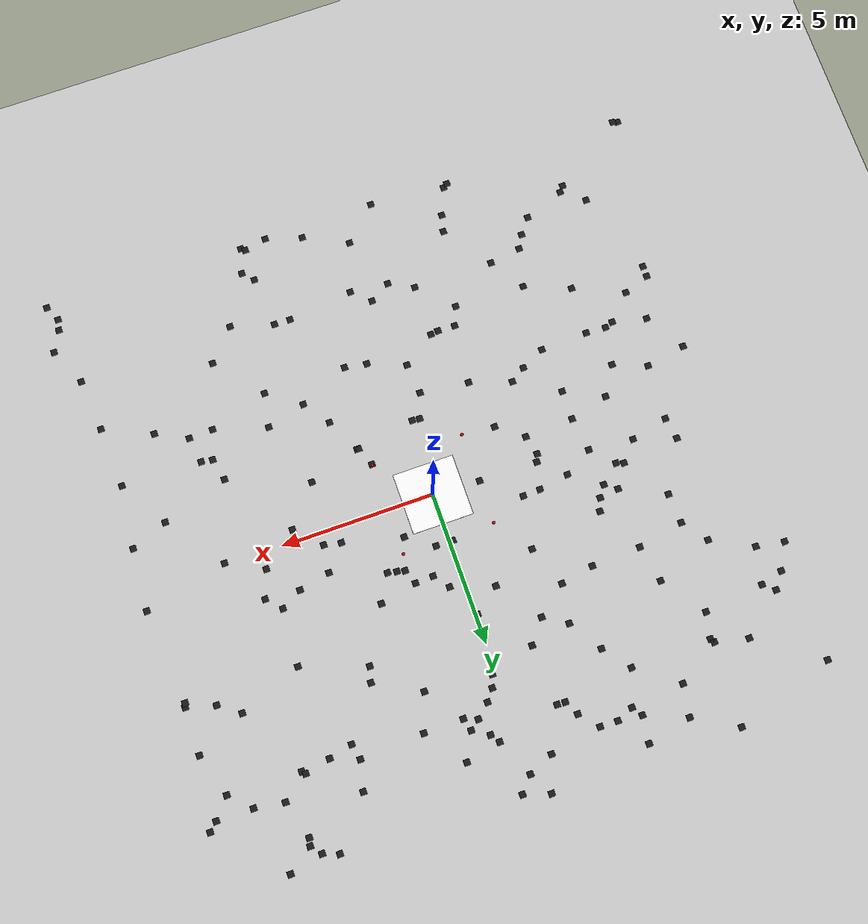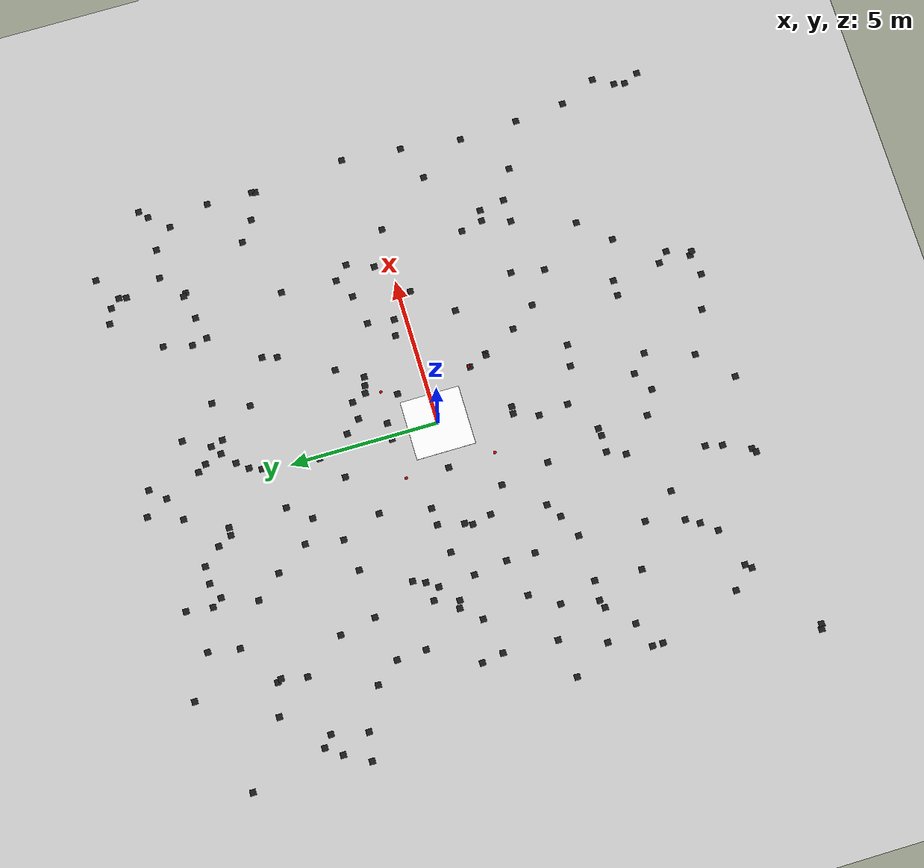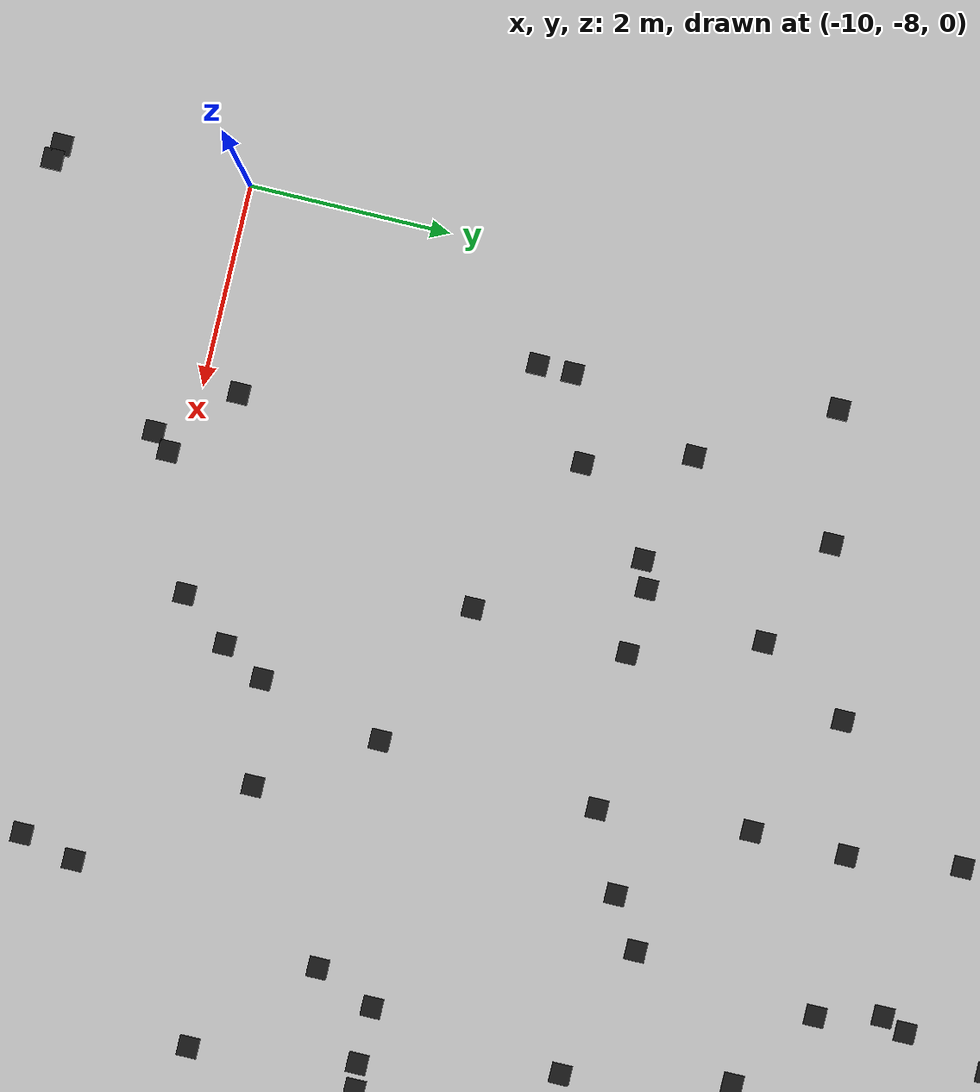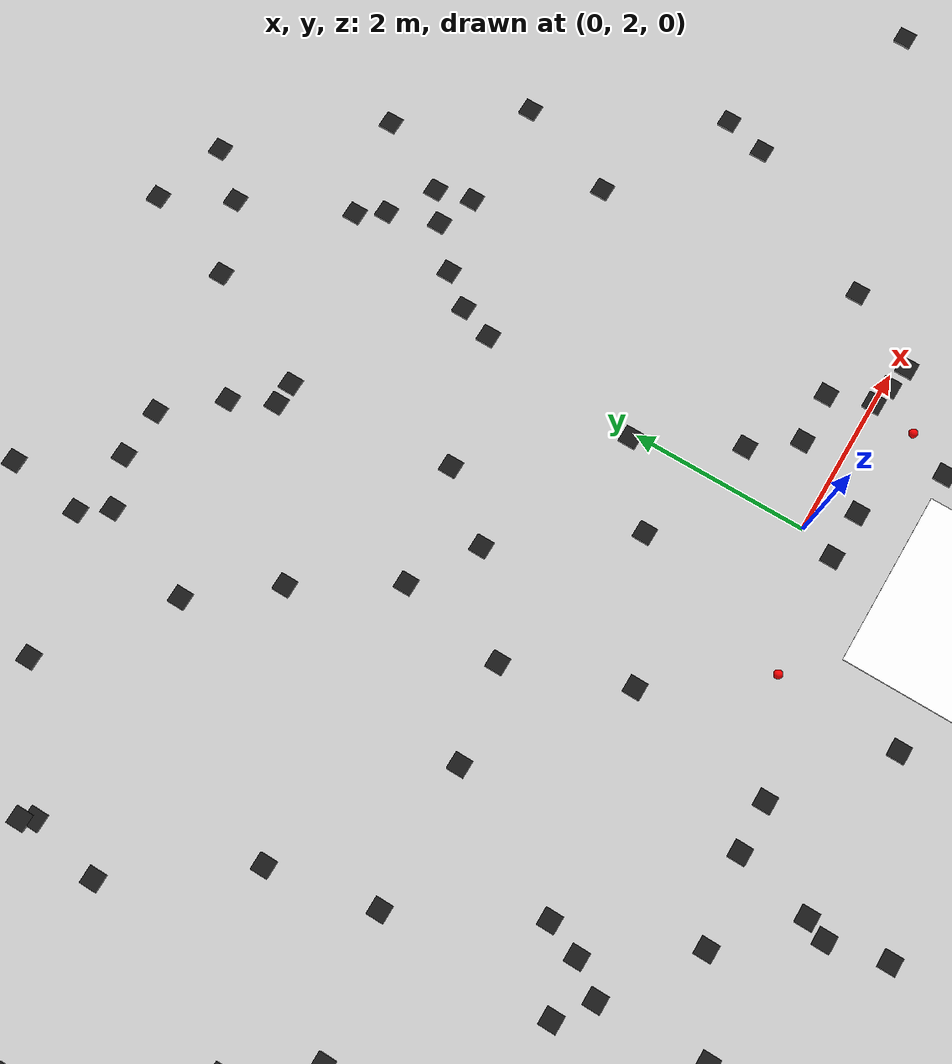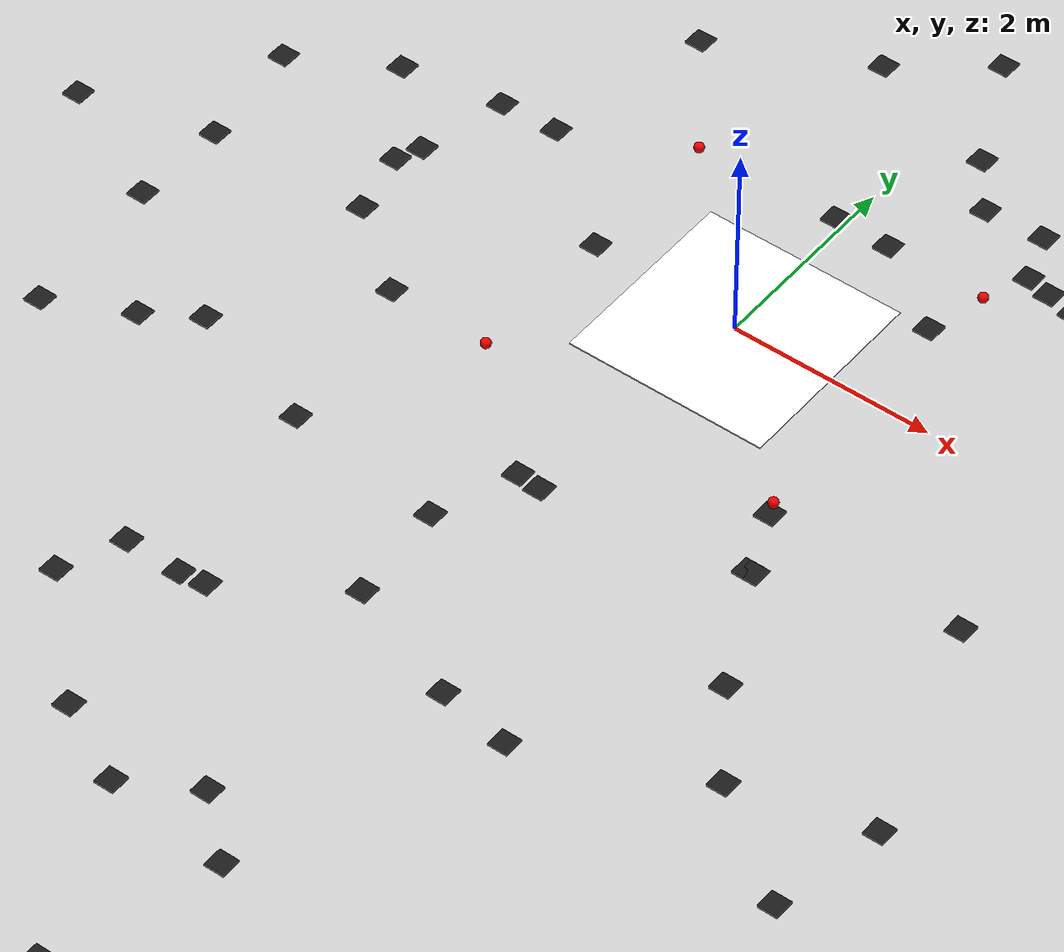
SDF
<?xml version="1.0" ?>
<sdf version="1.9">
  <world name="landing_world">
    <physics name="1ms" type="ignored">
      <max_step_size>0.001</max_step_size>
      <real_time_factor>1.0</real_time_factor>
    </physics>
    <plugin filename="gz-sim-physics-system" name="gz::sim::systems::Physics"></plugin>
    <plugin filename="gz-sim-user-commands-system" name="gz::sim::systems::UserCommands"></plugin>
    <plugin filename="gz-sim-scene-broadcaster-system" name="gz::sim::systems::SceneBroadcaster"></plugin>
    <plugin filename="gz-sim-sensors-system" name="gz::sim::systems::Sensors"><render_engine>ogre2</render_engine></plugin>
    <plugin filename="gz-sim-imu-system" name="gz::sim::systems::Imu"></plugin>
    <plugin filename="gz-sim-air-pressure-system" name="gz::sim::systems::AirPressure"></plugin>
    <plugin filename="gz-sim-air-speed-system" name="gz::sim::systems::AirSpeed"></plugin>
    <plugin filename="gz-sim-apply-link-wrench-system" name="gz::sim::systems::ApplyLinkWrench"></plugin>
    <plugin filename="gz-sim-magnetometer-system" name="gz::sim::systems::Magnetometer"></plugin>
    <plugin filename="gz-sim-navsat-system" name="gz::sim::systems::NavSat"></plugin>
    <plugin filename="gz-sim-contact-system" name="gz::sim::systems::Contact"></plugin>
    <plugin filename="libOpticalFlowSystem.so" name="custom::OpticalFlowSystem"></plugin>
    <plugin filename="libGstCameraSystem.so" name="custom::GstCameraSystem"></plugin>

    <light type="directional" name="sun">
      <cast_shadows>true</cast_shadows>
      <pose>0 0 10 0 0 0</pose>
      <diffuse>0.8 0.8 0.8 1</diffuse>
      <specular>0.2 0.2 0.2 1</specular>
      <attenuation><range>1000</range><constant>0.9</constant><linear>0.01</linear><quadratic>0.001</quadratic></attenuation>
      <direction>-0.5 0.1 -0.9</direction>
    </light>

    <model name="ground_plane">
      <static>true</static>
      <link name="link">
        <collision name="collision">
          <geometry><plane><normal>0 0 1</normal><size>100 100</size></plane></geometry>
        </collision>
        <visual name="visual">
          <geometry>
            <plane>
              <normal>0 0 1</normal>
              <size>100 100</size>
            </plane>
          </geometry>
          <material>
            <ambient>0.8 0.8 0.8 1</ambient>
            <diffuse>0.8 0.8 0.8 1</diffuse>
            <specular>0.1 0.1 0.1 1</specular>
            <pbr>
              <metal>
                <albedo_map>model://apriltag_pad/materials/textures/checkerboard.png</albedo_map>
              </metal>
            </pbr>
          </material>
        </visual>
      </link>
    </model>

    <!-- Anchor network around the target -->
    <include><uri>model://lora_anchor</uri><name>lora_anchor_0</name><pose>1.5 1.5 0.1 0 0 0</pose></include>
    <include><uri>model://lora_anchor</uri><name>lora_anchor_1</name><pose>1.5 -1.5 0.1 0 0 0</pose></include>
    <include><uri>model://lora_anchor</uri><name>lora_anchor_2</name><pose>-1.5 1.5 0.1 0 0 0</pose></include>
    <include><uri>model://lora_anchor</uri><name>lora_anchor_3</name><pose>-1.5 -1.5 0.1 0 0 0</pose></include>

    <!-- AprilTag Landing Pad (Local) -->
    <include>
      <name>apriltag_pad</name>
      <uri>model://apriltag_pad</uri>
      <pose>0 0 0.005 0 0 0</pose>
    </include>

    <model name="feature_box_1">
      <pose>6.064126727710061 -2.626235978707725 0.01 0 0 0</pose>
      <static>true</static>
      <link name="link">
        <visual name="visual">
          <geometry><box><size>0.2 0.2 0.02</size></box></geometry>
          <material>
            <ambient>0.1 0.1 0.1 1</ambient>
            <diffuse>0.1 0.1 0.1 1</diffuse>
          </material>
        </visual>
      </link>
    </model>
    <model name="feature_box_2">
      <pose>6.600908383867207 6.785454876282962 0.01 0 0 0</pose>
      <static>true</static>
      <link name="link">
        <visual name="visual">
          <geometry><box><size>0.2 0.2 0.02</size></box></geometry>
          <material>
            <ambient>0.1 0.1 0.1 1</ambient>
            <diffuse>0.1 0.1 0.1 1</diffuse>
          </material>
        </visual>
      </link>
    </model>
    <model name="feature_box_3">
      <pose>-9.909210892548927 5.062737538821175 0.01 0 0 0</pose>
      <static>true</static>
      <link name="link">
        <visual name="visual">
          <geometry><box><size>0.2 0.2 0.02</size></box></geometry>
          <material>
            <ambient>0.1 0.1 0.1 1</ambient>
            <diffuse>0.1 0.1 0.1 1</diffuse>
          </material>
        </visual>
      </link>
    </model>
    <model name="feature_box_4">
      <pose>9.770568118033758 -9.932839091898458 0.01 0 0 0</pose>
      <static>true</static>
      <link name="link">
        <visual name="visual">
          <geometry><box><size>0.2 0.2 0.02</size></box></geometry>
          <material>
            <ambient>0.1 0.1 0.1 1</ambient>
            <diffuse>0.1 0.1 0.1 1</diffuse>
          </material>
        </visual>
      </link>
    </model>
    <model name="feature_box_5">
      <pose>-7.065720062352973 3.427015625396715 0.01 0 0 0</pose>
      <static>true</static>
      <link name="link">
        <visual name="visual">
          <geometry><box><size>0.2 0.2 0.02</size></box></geometry>
          <material>
            <ambient>0.1 0.1 0.1 1</ambient>
            <diffuse>0.1 0.1 0.1 1</diffuse>
          </material>
        </visual>
      </link>
    </model>
    <model name="feature_box_6">
      <pose>-1.9289589729229348 -5.018895925553679 0.01 0 0 0</pose>
      <static>true</static>
      <link name="link">
        <visual name="visual">
          <geometry><box><size>0.2 0.2 0.02</size></box></geometry>
          <material>
            <ambient>0.1 0.1 0.1 1</ambient>
            <diffuse>0.1 0.1 0.1 1</diffuse>
          </material>
        </visual>
      </link>
    </model>
    <model name="feature_box_7">
      <pose>-0.8892170222058624 3.392100456258442 0.01 0 0 0</pose>
      <static>true</static>
      <link name="link">
        <visual name="visual">
          <geometry><box><size>0.2 0.2 0.02</size></box></geometry>
          <material>
            <ambient>0.1 0.1 0.1 1</ambient>
            <diffuse>0.1 0.1 0.1 1</diffuse>
          </material>
        </visual>
      </link>
    </model>
    <model name="feature_box_8">
      <pose>-4.1087346497789845 -2.949084905106913 0.01 0 0 0</pose>
      <static>true</static>
      <link name="link">
        <visual name="visual">
          <geometry><box><size>0.2 0.2 0.02</size></box></geometry>
          <material>
            <ambient>0.1 0.1 0.1 1</ambient>
            <diffuse>0.1 0.1 0.1 1</diffuse>
          </material>
        </visual>
      </link>
    </model>
    <model name="feature_box_9">
      <pose>0.6208670467753681 7.935946779149884 0.01 0 0 0</pose>
      <static>true</static>
      <link name="link">
        <visual name="visual">
          <geometry><box><size>0.2 0.2 0.02</size></box></geometry>
          <material>
            <ambient>0.1 0.1 0.1 1</ambient>
            <diffuse>0.1 0.1 0.1 1</diffuse>
          </material>
        </visual>
      </link>
    </model>
    <model name="feature_box_10">
      <pose>-2.744867911890938 -5.605769757853924 0.01 0 0 0</pose>
      <static>true</static>
      <link name="link">
        <visual name="visual">
          <geometry><box><size>0.2 0.2 0.02</size></box></geometry>
          <material>
            <ambient>0.1 0.1 0.1 1</ambient>
            <diffuse>0.1 0.1 0.1 1</diffuse>
          </material>
        </visual>
      </link>
    </model>
    <model name="feature_box_11">
      <pose>-7.016268590580072 2.4453357768004906 0.01 0 0 0</pose>
      <static>true</static>
      <link name="link">
        <visual name="visual">
          <geometry><box><size>0.2 0.2 0.02</size></box></geometry>
          <material>
            <ambient>0.1 0.1 0.1 1</ambient>
            <diffuse>0.1 0.1 0.1 1</diffuse>
          </material>
        </visual>
      </link>
    </model>
    <model name="feature_box_12">
      <pose>1.436211508465611 6.912990433453601 0.01 0 0 0</pose>
      <static>true</static>
      <link name="link">
        <visual name="visual">
          <geometry><box><size>0.2 0.2 0.02</size></box></geometry>
          <material>
            <ambient>0.1 0.1 0.1 1</ambient>
            <diffuse>0.1 0.1 0.1 1</diffuse>
          </material>
        </visual>
      </link>
    </model>
    <model name="feature_box_13">
      <pose>-2.641301640983656 5.240126960228045 0.01 0 0 0</pose>
      <static>true</static>
      <link name="link">
        <visual name="visual">
          <geometry><box><size>0.2 0.2 0.02</size></box></geometry>
          <material>
            <ambient>0.1 0.1 0.1 1</ambient>
            <diffuse>0.1 0.1 0.1 1</diffuse>
          </material>
        </visual>
      </link>
    </model>
    <model name="feature_box_14">
      <pose>4.912057851073353 1.501798716413564 0.01 0 0 0</pose>
      <static>true</static>
      <link name="link">
        <visual name="visual">
          <geometry><box><size>0.2 0.2 0.02</size></box></geometry>
          <material>
            <ambient>0.1 0.1 0.1 1</ambient>
            <diffuse>0.1 0.1 0.1 1</diffuse>
          </material>
        </visual>
      </link>
    </model>
    <model name="feature_box_15">
      <pose>-3.45252276005348 0.10106293615515582 0.01 0 0 0</pose>
      <static>true</static>
      <link name="link">
        <visual name="visual">
          <geometry><box><size>0.2 0.2 0.02</size></box></geometry>
          <material>
            <ambient>0.1 0.1 0.1 1</ambient>
            <diffuse>0.1 0.1 0.1 1</diffuse>
          </material>
        </visual>
      </link>
    </model>
    <model name="feature_box_16">
      <pose>9.282605964626097 -5.481513865361967 0.01 0 0 0</pose>
      <static>true</static>
      <link name="link">
        <visual name="visual">
          <geometry><box><size>0.2 0.2 0.02</size></box></geometry>
          <material>
            <ambient>0.1 0.1 0.1 1</ambient>
            <diffuse>0.1 0.1 0.1 1</diffuse>
          </material>
        </visual>
      </link>
    </model>
    <model name="feature_box_17">
      <pose>9.33291025835791 3.6518568073960935 0.01 0 0 0</pose>
      <static>true</static>
      <link name="link">
        <visual name="visual">
          <geometry><box><size>0.2 0.2 0.02</size></box></geometry>
          <material>
            <ambient>0.1 0.1 0.1 1</ambient>
            <diffuse>0.1 0.1 0.1 1</diffuse>
          </material>
        </visual>
      </link>
    </model>
    <model name="feature_box_18">
      <pose>3.4556407277400396 -8.961775679064194 0.01 0 0 0</pose>
      <static>true</static>
      <link name="link">
        <visual name="visual">
          <geometry><box><size>0.2 0.2 0.02</size></box></geometry>
          <material>
            <ambient>0.1 0.1 0.1 1</ambient>
            <diffuse>0.1 0.1 0.1 1</diffuse>
          </material>
        </visual>
      </link>
    </model>
    <model name="feature_box_19">
      <pose>-6.502419677279125 -4.946110899548895 0.01 0 0 0</pose>
      <static>true</static>
      <link name="link">
        <visual name="visual">
          <geometry><box><size>0.2 0.2 0.02</size></box></geometry>
          <material>
            <ambient>0.1 0.1 0.1 1</ambient>
            <diffuse>0.1 0.1 0.1 1</diffuse>
          </material>
        </visual>
      </link>
    </model>
    <model name="feature_box_20">
      <pose>3.7539360546442175 4.941706867919212 0.01 0 0 0</pose>
      <static>true</static>
      <link name="link">
        <visual name="visual">
          <geometry><box><size>0.2 0.2 0.02</size></box></geometry>
          <material>
            <ambient>0.1 0.1 0.1 1</ambient>
            <diffuse>0.1 0.1 0.1 1</diffuse>
          </material>
        </visual>
      </link>
    </model>
    <model name="feature_box_21">
      <pose>9.18744211042512 -3.4985291819596647 0.01 0 0 0</pose>
      <static>true</static>
      <link name="link">
        <visual name="visual">
          <geometry><box><size>0.2 0.2 0.02</size></box></geometry>
          <material>
            <ambient>0.1 0.1 0.1 1</ambient>
            <diffuse>0.1 0.1 0.1 1</diffuse>
          </material>
        </visual>
      </link>
    </model>
    <model name="feature_box_22">
      <pose>-4.226417569104672 0.8009666510185927 0.01 0 0 0</pose>
      <static>true</static>
      <link name="link">
        <visual name="visual">
          <geometry><box><size>0.2 0.2 0.02</size></box></geometry>
          <material>
            <ambient>0.1 0.1 0.1 1</ambient>
            <diffuse>0.1 0.1 0.1 1</diffuse>
          </material>
        </visual>
      </link>
    </model>
    <model name="feature_box_24">
      <pose>7.349379173035889 7.488834093403007 0.01 0 0 0</pose>
      <static>true</static>
      <link name="link">
        <visual name="visual">
          <geometry><box><size>0.2 0.2 0.02</size></box></geometry>
          <material>
            <ambient>0.1 0.1 0.1 1</ambient>
            <diffuse>0.1 0.1 0.1 1</diffuse>
          </material>
        </visual>
      </link>
    </model>
    <model name="feature_box_25">
      <pose>-1.9192961797643981 7.935140066157228 0.01 0 0 0</pose>
      <static>true</static>
      <link name="link">
        <visual name="visual">
          <geometry><box><size>0.2 0.2 0.02</size></box></geometry>
          <material>
            <ambient>0.1 0.1 0.1 1</ambient>
            <diffuse>0.1 0.1 0.1 1</diffuse>
          </material>
        </visual>
      </link>
    </model>
    <model name="feature_box_26">
      <pose>9.367858152609543 3.771719341284774 0.01 0 0 0</pose>
      <static>true</static>
      <link name="link">
        <visual name="visual">
          <geometry><box><size>0.2 0.2 0.02</size></box></geometry>
          <material>
            <ambient>0.1 0.1 0.1 1</ambient>
            <diffuse>0.1 0.1 0.1 1</diffuse>
          </material>
        </visual>
      </link>
    </model>
    <model name="feature_box_27">
      <pose>2.3409865623026 -3.289659595853558 0.01 0 0 0</pose>
      <static>true</static>
      <link name="link">
        <visual name="visual">
          <geometry><box><size>0.2 0.2 0.02</size></box></geometry>
          <material>
            <ambient>0.1 0.1 0.1 1</ambient>
            <diffuse>0.1 0.1 0.1 1</diffuse>
          </material>
        </visual>
      </link>
    </model>
    <model name="feature_box_28">
      <pose>-6.832608547639771 -2.10974772432591 0.01 0 0 0</pose>
      <static>true</static>
      <link name="link">
        <visual name="visual">
          <geometry><box><size>0.2 0.2 0.02</size></box></geometry>
          <material>
            <ambient>0.1 0.1 0.1 1</ambient>
            <diffuse>0.1 0.1 0.1 1</diffuse>
          </material>
        </visual>
      </link>
    </model>
    <model name="feature_box_29">
      <pose>8.242039872917047 -1.9275299290043257 0.01 0 0 0</pose>
      <static>true</static>
      <link name="link">
        <visual name="visual">
          <geometry><box><size>0.2 0.2 0.02</size></box></geometry>
          <material>
            <ambient>0.1 0.1 0.1 1</ambient>
            <diffuse>0.1 0.1 0.1 1</diffuse>
          </material>
        </visual>
      </link>
    </model>
    <model name="feature_box_30">
      <pose>-6.515880932768654 9.959481572674065 0.01 0 0 0</pose>
      <static>true</static>
      <link name="link">
        <visual name="visual">
          <geometry><box><size>0.2 0.2 0.02</size></box></geometry>
          <material>
            <ambient>0.1 0.1 0.1 1</ambient>
            <diffuse>0.1 0.1 0.1 1</diffuse>
          </material>
        </visual>
      </link>
    </model>
    <model name="feature_box_31">
      <pose>-6.5958419573035165 0.4139494941486461 0.01 0 0 0</pose>
      <static>true</static>
      <link name="link">
        <visual name="visual">
          <geometry><box><size>0.2 0.2 0.02</size></box></geometry>
          <material>
            <ambient>0.1 0.1 0.1 1</ambient>
            <diffuse>0.1 0.1 0.1 1</diffuse>
          </material>
        </visual>
      </link>
    </model>
    <model name="feature_box_32">
      <pose>4.214478121073725 -3.7805069073277187 0.01 0 0 0</pose>
      <static>true</static>
      <link name="link">
        <visual name="visual">
          <geometry><box><size>0.2 0.2 0.02</size></box></geometry>
          <material>
            <ambient>0.1 0.1 0.1 1</ambient>
            <diffuse>0.1 0.1 0.1 1</diffuse>
          </material>
        </visual>
      </link>
    </model>
    <model name="feature_box_33">
      <pose>-6.6745747351985045 7.2643908502468015 0.01 0 0 0</pose>
      <static>true</static>
      <link name="link">
        <visual name="visual">
          <geometry><box><size>0.2 0.2 0.02</size></box></geometry>
          <material>
            <ambient>0.1 0.1 0.1 1</ambient>
            <diffuse>0.1 0.1 0.1 1</diffuse>
          </material>
        </visual>
      </link>
    </model>
    <model name="feature_box_34">
      <pose>-1.6766963290722554 -4.9870986624706415 0.01 0 0 0</pose>
      <static>true</static>
      <link name="link">
        <visual name="visual">
          <geometry><box><size>0.2 0.2 0.02</size></box></geometry>
          <material>
            <ambient>0.1 0.1 0.1 1</ambient>
            <diffuse>0.1 0.1 0.1 1</diffuse>
          </material>
        </visual>
      </link>
    </model>
    <model name="feature_box_35">
      <pose>5.676968207673072 6.6971881112303535 0.01 0 0 0</pose>
      <static>true</static>
      <link name="link">
        <visual name="visual">
          <geometry><box><size>0.2 0.2 0.02</size></box></geometry>
          <material>
            <ambient>0.1 0.1 0.1 1</ambient>
            <diffuse>0.1 0.1 0.1 1</diffuse>
          </material>
        </visual>
      </link>
    </model>
    <model name="feature_box_36">
      <pose>-3.5551895789884957 8.297189750951933 0.01 0 0 0</pose>
      <static>true</static>
      <link name="link">
        <visual name="visual">
          <geometry><box><size>0.2 0.2 0.02</size></box></geometry>
          <material>
            <ambient>0.1 0.1 0.1 1</ambient>
            <diffuse>0.1 0.1 0.1 1</diffuse>
          </material>
        </visual>
      </link>
    </model>
    <model name="feature_box_37">
      <pose>-7.742137567008132 7.507112619388959 0.01 0 0 0</pose>
      <static>true</static>
      <link name="link">
        <visual name="visual">
          <geometry><box><size>0.2 0.2 0.02</size></box></geometry>
          <material>
            <ambient>0.1 0.1 0.1 1</ambient>
            <diffuse>0.1 0.1 0.1 1</diffuse>
          </material>
        </visual>
      </link>
    </model>
    <model name="feature_box_38">
      <pose>-1.5358275090488114 0.07458630154929935 0.01 0 0 0</pose>
      <static>true</static>
      <link name="link">
        <visual name="visual">
          <geometry><box><size>0.2 0.2 0.02</size></box></geometry>
          <material>
            <ambient>0.1 0.1 0.1 1</ambient>
            <diffuse>0.1 0.1 0.1 1</diffuse>
          </material>
        </visual>
      </link>
    </model>
    <model name="feature_box_39">
      <pose>-6.420954075885126 -3.3806348281609866 0.01 0 0 0</pose>
      <static>true</static>
      <link name="link">
        <visual name="visual">
          <geometry><box><size>0.2 0.2 0.02</size></box></geometry>
          <material>
            <ambient>0.1 0.1 0.1 1</ambient>
            <diffuse>0.1 0.1 0.1 1</diffuse>
          </material>
        </visual>
      </link>
    </model>
    <model name="feature_box_40">
      <pose>-6.775137355948733 6.304807291742172 0.01 0 0 0</pose>
      <static>true</static>
      <link name="link">
        <visual name="visual">
          <geometry><box><size>0.2 0.2 0.02</size></box></geometry>
          <material>
            <ambient>0.1 0.1 0.1 1</ambient>
            <diffuse>0.1 0.1 0.1 1</diffuse>
          </material>
        </visual>
      </link>
    </model>
    <model name="feature_box_41">
      <pose>-3.6634679774241246 9.489724624098997 0.01 0 0 0</pose>
      <static>true</static>
      <link name="link">
        <visual name="visual">
          <geometry><box><size>0.2 0.2 0.02</size></box></geometry>
          <material>
            <ambient>0.1 0.1 0.1 1</ambient>
            <diffuse>0.1 0.1 0.1 1</diffuse>
          </material>
        </visual>
      </link>
    </model>
    <model name="feature_box_42">
      <pose>3.7648382686285444 0.3971200652457867 0.01 0 0 0</pose>
      <static>true</static>
      <link name="link">
        <visual name="visual">
          <geometry><box><size>0.2 0.2 0.02</size></box></geometry>
          <material>
            <ambient>0.1 0.1 0.1 1</ambient>
            <diffuse>0.1 0.1 0.1 1</diffuse>
          </material>
        </visual>
      </link>
    </model>
    <model name="feature_box_43">
      <pose>0.45107981766839167 1.5890589341092092 0.01 0 0 0</pose>
      <static>true</static>
      <link name="link">
        <visual name="visual">
          <geometry><box><size>0.2 0.2 0.02</size></box></geometry>
          <material>
            <ambient>0.1 0.1 0.1 1</ambient>
            <diffuse>0.1 0.1 0.1 1</diffuse>
          </material>
        </visual>
      </link>
    </model>
    <model name="feature_box_44">
      <pose>-7.304109062610024 -8.183303469342878 0.01 0 0 0</pose>
      <static>true</static>
      <link name="link">
        <visual name="visual">
          <geometry><box><size>0.2 0.2 0.02</size></box></geometry>
          <material>
            <ambient>0.1 0.1 0.1 1</ambient>
            <diffuse>0.1 0.1 0.1 1</diffuse>
          </material>
        </visual>
      </link>
    </model>
    <model name="feature_box_45">
      <pose>-7.809036345069922 0.12285730443652909 0.01 0 0 0</pose>
      <static>true</static>
      <link name="link">
        <visual name="visual">
          <geometry><box><size>0.2 0.2 0.02</size></box></geometry>
          <material>
            <ambient>0.1 0.1 0.1 1</ambient>
            <diffuse>0.1 0.1 0.1 1</diffuse>
          </material>
        </visual>
      </link>
    </model>
    <model name="feature_box_47">
      <pose>5.031324332224687 7.970569277996113 0.01 0 0 0</pose>
      <static>true</static>
      <link name="link">
        <visual name="visual">
          <geometry><box><size>0.2 0.2 0.02</size></box></geometry>
          <material>
            <ambient>0.1 0.1 0.1 1</ambient>
            <diffuse>0.1 0.1 0.1 1</diffuse>
          </material>
        </visual>
      </link>
    </model>
    <model name="feature_box_48">
      <pose>6.587484761806252 -3.413515060821637 0.01 0 0 0</pose>
      <static>true</static>
      <link name="link">
        <visual name="visual">
          <geometry><box><size>0.2 0.2 0.02</size></box></geometry>
          <material>
            <ambient>0.1 0.1 0.1 1</ambient>
            <diffuse>0.1 0.1 0.1 1</diffuse>
          </material>
        </visual>
      </link>
    </model>
    <model name="feature_box_49">
      <pose>-0.7458317283458467 8.800610048963026 0.01 0 0 0</pose>
      <static>true</static>
      <link name="link">
        <visual name="visual">
          <geometry><box><size>0.2 0.2 0.02</size></box></geometry>
          <material>
            <ambient>0.1 0.1 0.1 1</ambient>
            <diffuse>0.1 0.1 0.1 1</diffuse>
          </material>
        </visual>
      </link>
    </model>
    <model name="feature_box_50">
      <pose>1.0070002379723402 7.076137716043604 0.01 0 0 0</pose>
      <static>true</static>
      <link name="link">
        <visual name="visual">
          <geometry><box><size>0.2 0.2 0.02</size></box></geometry>
          <material>
            <ambient>0.1 0.1 0.1 1</ambient>
            <diffuse>0.1 0.1 0.1 1</diffuse>
          </material>
        </visual>
      </link>
    </model>
    <model name="feature_box_51">
      <pose>-9.775491908221047 8.93046403598872 0.01 0 0 0</pose>
      <static>true</static>
      <link name="link">
        <visual name="visual">
          <geometry><box><size>0.2 0.2 0.02</size></box></geometry>
          <material>
            <ambient>0.1 0.1 0.1 1</ambient>
            <diffuse>0.1 0.1 0.1 1</diffuse>
          </material>
        </visual>
      </link>
    </model>
    <model name="feature_box_52">
      <pose>-2.2838961415750685 -3.0708959945929903 0.01 0 0 0</pose>
      <static>true</static>
      <link name="link">
        <visual name="visual">
          <geometry><box><size>0.2 0.2 0.02</size></box></geometry>
          <material>
            <ambient>0.1 0.1 0.1 1</ambient>
            <diffuse>0.1 0.1 0.1 1</diffuse>
          </material>
        </visual>
      </link>
    </model>
    <model name="feature_box_53">
      <pose>5.59395685474003 1.8774813221426392 0.01 0 0 0</pose>
      <static>true</static>
      <link name="link">
        <visual name="visual">
          <geometry><box><size>0.2 0.2 0.02</size></box></geometry>
          <material>
            <ambient>0.1 0.1 0.1 1</ambient>
            <diffuse>0.1 0.1 0.1 1</diffuse>
          </material>
        </visual>
      </link>
    </model>
    <model name="feature_box_54">
      <pose>-5.041003270683344 -5.529070991417811 0.01 0 0 0</pose>
      <static>true</static>
      <link name="link">
        <visual name="visual">
          <geometry><box><size>0.2 0.2 0.02</size></box></geometry>
          <material>
            <ambient>0.1 0.1 0.1 1</ambient>
            <diffuse>0.1 0.1 0.1 1</diffuse>
          </material>
        </visual>
      </link>
    </model>
    <model name="feature_box_55">
      <pose>-5.119987024611634 9.160143684232743 0.01 0 0 0</pose>
      <static>true</static>
      <link name="link">
        <visual name="visual">
          <geometry><box><size>0.2 0.2 0.02</size></box></geometry>
          <material>
            <ambient>0.1 0.1 0.1 1</ambient>
            <diffuse>0.1 0.1 0.1 1</diffuse>
          </material>
        </visual>
      </link>
    </model>
    <model name="feature_box_56">
      <pose>-0.1699671239294922 -2.483087863056994 0.01 0 0 0</pose>
      <static>true</static>
      <link name="link">
        <visual name="visual">
          <geometry><box><size>0.2 0.2 0.02</size></box></geometry>
          <material>
            <ambient>0.1 0.1 0.1 1</ambient>
            <diffuse>0.1 0.1 0.1 1</diffuse>
          </material>
        </visual>
      </link>
    </model>
    <model name="feature_box_57">
      <pose>-7.075771792286163 -3.3432625768633333 0.01 0 0 0</pose>
      <static>true</static>
      <link name="link">
        <visual name="visual">
          <geometry><box><size>0.2 0.2 0.02</size></box></geometry>
          <material>
            <ambient>0.1 0.1 0.1 1</ambient>
            <diffuse>0.1 0.1 0.1 1</diffuse>
          </material>
        </visual>
      </link>
    </model>
    <model name="feature_box_58">
      <pose>-5.599321693203992 -7.215405734531865 0.01 0 0 0</pose>
      <static>true</static>
      <link name="link">
        <visual name="visual">
          <geometry><box><size>0.2 0.2 0.02</size></box></geometry>
          <material>
            <ambient>0.1 0.1 0.1 1</ambient>
            <diffuse>0.1 0.1 0.1 1</diffuse>
          </material>
        </visual>
      </link>
    </model>
    <model name="feature_box_59">
      <pose>9.609454935898434 0.5563756015819248 0.01 0 0 0</pose>
      <static>true</static>
      <link name="link">
        <visual name="visual">
          <geometry><box><size>0.2 0.2 0.02</size></box></geometry>
          <material>
            <ambient>0.1 0.1 0.1 1</ambient>
            <diffuse>0.1 0.1 0.1 1</diffuse>
          </material>
        </visual>
      </link>
    </model>
    <model name="feature_box_60">
      <pose>0.5670516229045006 6.684000291254854 0.01 0 0 0</pose>
      <static>true</static>
      <link name="link">
        <visual name="visual">
          <geometry><box><size>0.2 0.2 0.02</size></box></geometry>
          <material>
            <ambient>0.1 0.1 0.1 1</ambient>
            <diffuse>0.1 0.1 0.1 1</diffuse>
          </material>
        </visual>
      </link>
    </model>
    <model name="feature_box_61">
      <pose>1.5048151518458184 -1.5531711853770531 0.01 0 0 0</pose>
      <static>true</static>
      <link name="link">
        <visual name="visual">
          <geometry><box><size>0.2 0.2 0.02</size></box></geometry>
          <material>
            <ambient>0.1 0.1 0.1 1</ambient>
            <diffuse>0.1 0.1 0.1 1</diffuse>
          </material>
        </visual>
      </link>
    </model>
    <model name="feature_box_62">
      <pose>-3.7329664444424253 -9.601923670663963 0.01 0 0 0</pose>
      <static>true</static>
      <link name="link">
        <visual name="visual">
          <geometry><box><size>0.2 0.2 0.02</size></box></geometry>
          <material>
            <ambient>0.1 0.1 0.1 1</ambient>
            <diffuse>0.1 0.1 0.1 1</diffuse>
          </material>
        </visual>
      </link>
    </model>
    <model name="feature_box_63">
      <pose>0.06855046370515439 9.154062740184095 0.01 0 0 0</pose>
      <static>true</static>
      <link name="link">
        <visual name="visual">
          <geometry><box><size>0.2 0.2 0.02</size></box></geometry>
          <material>
            <ambient>0.1 0.1 0.1 1</ambient>
            <diffuse>0.1 0.1 0.1 1</diffuse>
          </material>
        </visual>
      </link>
    </model>
    <model name="feature_box_64">
      <pose>0.2845614107977781 6.323363278706335 0.01 0 0 0</pose>
      <static>true</static>
      <link name="link">
        <visual name="visual">
          <geometry><box><size>0.2 0.2 0.02</size></box></geometry>
          <material>
            <ambient>0.1 0.1 0.1 1</ambient>
            <diffuse>0.1 0.1 0.1 1</diffuse>
          </material>
        </visual>
      </link>
    </model>
    <model name="feature_box_65">
      <pose>-8.118908838300122 -4.232252966555445 0.01 0 0 0</pose>
      <static>true</static>
      <link name="link">
        <visual name="visual">
          <geometry><box><size>0.2 0.2 0.02</size></box></geometry>
          <material>
            <ambient>0.1 0.1 0.1 1</ambient>
            <diffuse>0.1 0.1 0.1 1</diffuse>
          </material>
        </visual>
      </link>
    </model>
    <model name="feature_box_66">
      <pose>-9.460781128736961 5.885304300718271 0.01 0 0 0</pose>
      <static>true</static>
      <link name="link">
        <visual name="visual">
          <geometry><box><size>0.2 0.2 0.02</size></box></geometry>
          <material>
            <ambient>0.1 0.1 0.1 1</ambient>
            <diffuse>0.1 0.1 0.1 1</diffuse>
          </material>
        </visual>
      </link>
    </model>
    <model name="feature_box_67">
      <pose>-0.19282635161419037 -8.801551305537082 0.01 0 0 0</pose>
      <static>true</static>
      <link name="link">
        <visual name="visual">
          <geometry><box><size>0.2 0.2 0.02</size></box></geometry>
          <material>
            <ambient>0.1 0.1 0.1 1</ambient>
            <diffuse>0.1 0.1 0.1 1</diffuse>
          </material>
        </visual>
      </link>
    </model>
    <model name="feature_box_68">
      <pose>-5.7934105970678935 4.934970086348313 0.01 0 0 0</pose>
      <static>true</static>
      <link name="link">
        <visual name="visual">
          <geometry><box><size>0.2 0.2 0.02</size></box></geometry>
          <material>
            <ambient>0.1 0.1 0.1 1</ambient>
            <diffuse>0.1 0.1 0.1 1</diffuse>
          </material>
        </visual>
      </link>
    </model>
    <model name="feature_box_69">
      <pose>-1.7074703787140493 -6.657728517892578 0.01 0 0 0</pose>
      <static>true</static>
      <link name="link">
        <visual name="visual">
          <geometry><box><size>0.2 0.2 0.02</size></box></geometry>
          <material>
            <ambient>0.1 0.1 0.1 1</ambient>
            <diffuse>0.1 0.1 0.1 1</diffuse>
          </material>
        </visual>
      </link>
    </model>
    <model name="feature_box_70">
      <pose>-0.611275003136937 -4.268085017473961 0.01 0 0 0</pose>
      <static>true</static>
      <link name="link">
        <visual name="visual">
          <geometry><box><size>0.2 0.2 0.02</size></box></geometry>
          <material>
            <ambient>0.1 0.1 0.1 1</ambient>
            <diffuse>0.1 0.1 0.1 1</diffuse>
          </material>
        </visual>
      </link>
    </model>
    <model name="feature_box_72">
      <pose>-2.6726392182653953 0.9918294032522788 0.01 0 0 0</pose>
      <static>true</static>
      <link name="link">
        <visual name="visual">
          <geometry><box><size>0.2 0.2 0.02</size></box></geometry>
          <material>
            <ambient>0.1 0.1 0.1 1</ambient>
            <diffuse>0.1 0.1 0.1 1</diffuse>
          </material>
        </visual>
      </link>
    </model>
    <model name="feature_box_73">
      <pose>2.984058012711106 -6.9678447055918795 0.01 0 0 0</pose>
      <static>true</static>
      <link name="link">
        <visual name="visual">
          <geometry><box><size>0.2 0.2 0.02</size></box></geometry>
          <material>
            <ambient>0.1 0.1 0.1 1</ambient>
            <diffuse>0.1 0.1 0.1 1</diffuse>
          </material>
        </visual>
      </link>
    </model>
    <model name="feature_box_74">
      <pose>-3.5532248880131245 -0.14370077677978443 0.01 0 0 0</pose>
      <static>true</static>
      <link name="link">
        <visual name="visual">
          <geometry><box><size>0.2 0.2 0.02</size></box></geometry>
          <material>
            <ambient>0.1 0.1 0.1 1</ambient>
            <diffuse>0.1 0.1 0.1 1</diffuse>
          </material>
        </visual>
      </link>
    </model>
    <model name="feature_box_75">
      <pose>4.911367645432401 6.51567170236207 0.01 0 0 0</pose>
      <static>true</static>
      <link name="link">
        <visual name="visual">
          <geometry><box><size>0.2 0.2 0.02</size></box></geometry>
          <material>
            <ambient>0.1 0.1 0.1 1</ambient>
            <diffuse>0.1 0.1 0.1 1</diffuse>
          </material>
        </visual>
      </link>
    </model>
    <model name="feature_box_76">
      <pose>-3.6207341098160395 -2.6335918704440147 0.01 0 0 0</pose>
      <static>true</static>
      <link name="link">
        <visual name="visual">
          <geometry><box><size>0.2 0.2 0.02</size></box></geometry>
          <material>
            <ambient>0.1 0.1 0.1 1</ambient>
            <diffuse>0.1 0.1 0.1 1</diffuse>
          </material>
        </visual>
      </link>
    </model>
    <model name="feature_box_77">
      <pose>2.3722537458844286 -9.840938349179737 0.01 0 0 0</pose>
      <static>true</static>
      <link name="link">
        <visual name="visual">
          <geometry><box><size>0.2 0.2 0.02</size></box></geometry>
          <material>
            <ambient>0.1 0.1 0.1 1</ambient>
            <diffuse>0.1 0.1 0.1 1</diffuse>
          </material>
        </visual>
      </link>
    </model>
    <model name="feature_box_78">
      <pose>-0.4108767335065444 -2.460865361253097 0.01 0 0 0</pose>
      <static>true</static>
      <link name="link">
        <visual name="visual">
          <geometry><box><size>0.2 0.2 0.02</size></box></geometry>
          <material>
            <ambient>0.1 0.1 0.1 1</ambient>
            <diffuse>0.1 0.1 0.1 1</diffuse>
          </material>
        </visual>
      </link>
    </model>
    <model name="feature_box_79">
      <pose>8.43904074719623 4.034419335192377 0.01 0 0 0</pose>
      <static>true</static>
      <link name="link">
        <visual name="visual">
          <geometry><box><size>0.2 0.2 0.02</size></box></geometry>
          <material>
            <ambient>0.1 0.1 0.1 1</ambient>
            <diffuse>0.1 0.1 0.1 1</diffuse>
          </material>
        </visual>
      </link>
    </model>
    <model name="feature_box_80">
      <pose>-3.946855501420032 3.7950392875429966 0.01 0 0 0</pose>
      <static>true</static>
      <link name="link">
        <visual name="visual">
          <geometry><box><size>0.2 0.2 0.02</size></box></geometry>
          <material>
            <ambient>0.1 0.1 0.1 1</ambient>
            <diffuse>0.1 0.1 0.1 1</diffuse>
          </material>
        </visual>
      </link>
    </model>
    <model name="feature_box_81">
      <pose>6.784245414227978 9.289140177789747 0.01 0 0 0</pose>
      <static>true</static>
      <link name="link">
        <visual name="visual">
          <geometry><box><size>0.2 0.2 0.02</size></box></geometry>
          <material>
            <ambient>0.1 0.1 0.1 1</ambient>
            <diffuse>0.1 0.1 0.1 1</diffuse>
          </material>
        </visual>
      </link>
    </model>
    <model name="feature_box_82">
      <pose>0.8150496666156375 7.6468724504617605 0.01 0 0 0</pose>
      <static>true</static>
      <link name="link">
        <visual name="visual">
          <geometry><box><size>0.2 0.2 0.02</size></box></geometry>
          <material>
            <ambient>0.1 0.1 0.1 1</ambient>
            <diffuse>0.1 0.1 0.1 1</diffuse>
          </material>
        </visual>
      </link>
    </model>
    <model name="feature_box_83">
      <pose>1.7688166084067714 8.183691301772374 0.01 0 0 0</pose>
      <static>true</static>
      <link name="link">
        <visual name="visual">
          <geometry><box><size>0.2 0.2 0.02</size></box></geometry>
          <material>
            <ambient>0.1 0.1 0.1 1</ambient>
            <diffuse>0.1 0.1 0.1 1</diffuse>
          </material>
        </visual>
      </link>
    </model>
    <model name="feature_box_84">
      <pose>-0.2484281920590945 -6.679318797436597 0.01 0 0 0</pose>
      <static>true</static>
      <link name="link">
        <visual name="visual">
          <geometry><box><size>0.2 0.2 0.02</size></box></geometry>
          <material>
            <ambient>0.1 0.1 0.1 1</ambient>
            <diffuse>0.1 0.1 0.1 1</diffuse>
          </material>
        </visual>
      </link>
    </model>
    <model name="feature_box_86">
      <pose>5.701876252006276 0.5289654910223263 0.01 0 0 0</pose>
      <static>true</static>
      <link name="link">
        <visual name="visual">
          <geometry><box><size>0.2 0.2 0.02</size></box></geometry>
          <material>
            <ambient>0.1 0.1 0.1 1</ambient>
            <diffuse>0.1 0.1 0.1 1</diffuse>
          </material>
        </visual>
      </link>
    </model>
    <model name="feature_box_87">
      <pose>9.391704488357359 5.304789859146785 0.01 0 0 0</pose>
      <static>true</static>
      <link name="link">
        <visual name="visual">
          <geometry><box><size>0.2 0.2 0.02</size></box></geometry>
          <material>
            <ambient>0.1 0.1 0.1 1</ambient>
            <diffuse>0.1 0.1 0.1 1</diffuse>
          </material>
        </visual>
      </link>
    </model>
    <model name="feature_box_88">
      <pose>-5.561249105859176 3.7286766120073533 0.01 0 0 0</pose>
      <static>true</static>
      <link name="link">
        <visual name="visual">
          <geometry><box><size>0.2 0.2 0.02</size></box></geometry>
          <material>
            <ambient>0.1 0.1 0.1 1</ambient>
            <diffuse>0.1 0.1 0.1 1</diffuse>
          </material>
        </visual>
      </link>
    </model>
    <model name="feature_box_89">
      <pose>-2.494462322839195 -5.006004894333175 0.01 0 0 0</pose>
      <static>true</static>
      <link name="link">
        <visual name="visual">
          <geometry><box><size>0.2 0.2 0.02</size></box></geometry>
          <material>
            <ambient>0.1 0.1 0.1 1</ambient>
            <diffuse>0.1 0.1 0.1 1</diffuse>
          </material>
        </visual>
      </link>
    </model>
    <model name="feature_box_90">
      <pose>-5.990096194120895 -7.707234748397163 0.01 0 0 0</pose>
      <static>true</static>
      <link name="link">
        <visual name="visual">
          <geometry><box><size>0.2 0.2 0.02</size></box></geometry>
          <material>
            <ambient>0.1 0.1 0.1 1</ambient>
            <diffuse>0.1 0.1 0.1 1</diffuse>
          </material>
        </visual>
      </link>
    </model>
    <model name="feature_box_91">
      <pose>-2.5775663538755396 -1.4203323091407718 0.01 0 0 0</pose>
      <static>true</static>
      <link name="link">
        <visual name="visual">
          <geometry><box><size>0.2 0.2 0.02</size></box></geometry>
          <material>
            <ambient>0.1 0.1 0.1 1</ambient>
            <diffuse>0.1 0.1 0.1 1</diffuse>
          </material>
        </visual>
      </link>
    </model>
    <model name="feature_box_92">
      <pose>5.719205239278605 3.7335593552198993 0.01 0 0 0</pose>
      <static>true</static>
      <link name="link">
        <visual name="visual">
          <geometry><box><size>0.2 0.2 0.02</size></box></geometry>
          <material>
            <ambient>0.1 0.1 0.1 1</ambient>
            <diffuse>0.1 0.1 0.1 1</diffuse>
          </material>
        </visual>
      </link>
    </model>
    <model name="feature_box_93">
      <pose>7.769955172493461 4.519361079293311 0.01 0 0 0</pose>
      <static>true</static>
      <link name="link">
        <visual name="visual">
          <geometry><box><size>0.2 0.2 0.02</size></box></geometry>
          <material>
            <ambient>0.1 0.1 0.1 1</ambient>
            <diffuse>0.1 0.1 0.1 1</diffuse>
          </material>
        </visual>
      </link>
    </model>
    <model name="feature_box_94">
      <pose>4.3646386098028085 -7.370816275899495 0.01 0 0 0</pose>
      <static>true</static>
      <link name="link">
        <visual name="visual">
          <geometry><box><size>0.2 0.2 0.02</size></box></geometry>
          <material>
            <ambient>0.1 0.1 0.1 1</ambient>
            <diffuse>0.1 0.1 0.1 1</diffuse>
          </material>
        </visual>
      </link>
    </model>
    <model name="feature_box_95">
      <pose>9.438310888267893 -1.460821576930666 0.01 0 0 0</pose>
      <static>true</static>
      <link name="link">
        <visual name="visual">
          <geometry><box><size>0.2 0.2 0.02</size></box></geometry>
          <material>
            <ambient>0.1 0.1 0.1 1</ambient>
            <diffuse>0.1 0.1 0.1 1</diffuse>
          </material>
        </visual>
      </link>
    </model>
    <model name="feature_box_96">
      <pose>4.803347423795618 7.03052984371347 0.01 0 0 0</pose>
      <static>true</static>
      <link name="link">
        <visual name="visual">
          <geometry><box><size>0.2 0.2 0.02</size></box></geometry>
          <material>
            <ambient>0.1 0.1 0.1 1</ambient>
            <diffuse>0.1 0.1 0.1 1</diffuse>
          </material>
        </visual>
      </link>
    </model>
    <model name="feature_box_97">
      <pose>-1.4226758429963695 7.456606901951098 0.01 0 0 0</pose>
      <static>true</static>
      <link name="link">
        <visual name="visual">
          <geometry><box><size>0.2 0.2 0.02</size></box></geometry>
          <material>
            <ambient>0.1 0.1 0.1 1</ambient>
            <diffuse>0.1 0.1 0.1 1</diffuse>
          </material>
        </visual>
      </link>
    </model>
    <model name="feature_box_98">
      <pose>-1.8986099639924632 4.777676132977843 0.01 0 0 0</pose>
      <static>true</static>
      <link name="link">
        <visual name="visual">
          <geometry><box><size>0.2 0.2 0.02</size></box></geometry>
          <material>
            <ambient>0.1 0.1 0.1 1</ambient>
            <diffuse>0.1 0.1 0.1 1</diffuse>
          </material>
        </visual>
      </link>
    </model>
    <model name="feature_box_99">
      <pose>6.5076923719978055 6.884529101351841 0.01 0 0 0</pose>
      <static>true</static>
      <link name="link">
        <visual name="visual">
          <geometry><box><size>0.2 0.2 0.02</size></box></geometry>
          <material>
            <ambient>0.1 0.1 0.1 1</ambient>
            <diffuse>0.1 0.1 0.1 1</diffuse>
          </material>
        </visual>
      </link>
    </model>
    <model name="feature_box_100">
      <pose>6.874755345130389 -0.07562361492452396 0.01 0 0 0</pose>
      <static>true</static>
      <link name="link">
        <visual name="visual">
          <geometry><box><size>0.2 0.2 0.02</size></box></geometry>
          <material>
            <ambient>0.1 0.1 0.1 1</ambient>
            <diffuse>0.1 0.1 0.1 1</diffuse>
          </material>
        </visual>
      </link>
    </model>
    <model name="feature_box_101">
      <pose>-1.6845046236108967 7.4670158676055145 0.01 0 0 0</pose>
      <static>true</static>
      <link name="link">
        <visual name="visual">
          <geometry><box><size>0.2 0.2 0.02</size></box></geometry>
          <material>
            <ambient>0.1 0.1 0.1 1</ambient>
            <diffuse>0.1 0.1 0.1 1</diffuse>
          </material>
        </visual>
      </link>
    </model>
    <model name="feature_box_102">
      <pose>0.8572251902297836 2.455811284757594 0.01 0 0 0</pose>
      <static>true</static>
      <link name="link">
        <visual name="visual">
          <geometry><box><size>0.2 0.2 0.02</size></box></geometry>
          <material>
            <ambient>0.1 0.1 0.1 1</ambient>
            <diffuse>0.1 0.1 0.1 1</diffuse>
          </material>
        </visual>
      </link>
    </model>
    <model name="feature_box_103">
      <pose>-3.88079817673116 -9.696979443749594 0.01 0 0 0</pose>
      <static>true</static>
      <link name="link">
        <visual name="visual">
          <geometry><box><size>0.2 0.2 0.02</size></box></geometry>
          <material>
            <ambient>0.1 0.1 0.1 1</ambient>
            <diffuse>0.1 0.1 0.1 1</diffuse>
          </material>
        </visual>
      </link>
    </model>
    <model name="feature_box_104">
      <pose>-5.145654441932221 0.27582057556330497 0.01 0 0 0</pose>
      <static>true</static>
      <link name="link">
        <visual name="visual">
          <geometry><box><size>0.2 0.2 0.02</size></box></geometry>
          <material>
            <ambient>0.1 0.1 0.1 1</ambient>
            <diffuse>0.1 0.1 0.1 1</diffuse>
          </material>
        </visual>
      </link>
    </model>
    <model name="feature_box_105">
      <pose>3.2226052081144037 0.5089127132642997 0.01 0 0 0</pose>
      <static>true</static>
      <link name="link">
        <visual name="visual">
          <geometry><box><size>0.2 0.2 0.02</size></box></geometry>
          <material>
            <ambient>0.1 0.1 0.1 1</ambient>
            <diffuse>0.1 0.1 0.1 1</diffuse>
          </material>
        </visual>
      </link>
    </model>
    <model name="feature_box_106">
      <pose>-9.208488197235303 -1.9273587206219567 0.01 0 0 0</pose>
      <static>true</static>
      <link name="link">
        <visual name="visual">
          <geometry><box><size>0.2 0.2 0.02</size></box></geometry>
          <material>
            <ambient>0.1 0.1 0.1 1</ambient>
            <diffuse>0.1 0.1 0.1 1</diffuse>
          </material>
        </visual>
      </link>
    </model>
    <model name="feature_box_107">
      <pose>8.966311074081478 6.706018887743866 0.01 0 0 0</pose>
      <static>true</static>
      <link name="link">
        <visual name="visual">
          <geometry><box><size>0.2 0.2 0.02</size></box></geometry>
          <material>
            <ambient>0.1 0.1 0.1 1</ambient>
            <diffuse>0.1 0.1 0.1 1</diffuse>
          </material>
        </visual>
      </link>
    </model>
    <model name="feature_box_108">
      <pose>9.428077595188963 -7.184857674474559 0.01 0 0 0</pose>
      <static>true</static>
      <link name="link">
        <visual name="visual">
          <geometry><box><size>0.2 0.2 0.02</size></box></geometry>
          <material>
            <ambient>0.1 0.1 0.1 1</ambient>
            <diffuse>0.1 0.1 0.1 1</diffuse>
          </material>
        </visual>
      </link>
    </model>
    <model name="feature_box_109">
      <pose>2.290235727429417 5.739911009278432 0.01 0 0 0</pose>
      <static>true</static>
      <link name="link">
        <visual name="visual">
          <geometry><box><size>0.2 0.2 0.02</size></box></geometry>
          <material>
            <ambient>0.1 0.1 0.1 1</ambient>
            <diffuse>0.1 0.1 0.1 1</diffuse>
          </material>
        </visual>
      </link>
    </model>
    <model name="feature_box_110">
      <pose>-3.7753429729923793 8.618285537138398 0.01 0 0 0</pose>
      <static>true</static>
      <link name="link">
        <visual name="visual">
          <geometry><box><size>0.2 0.2 0.02</size></box></geometry>
          <material>
            <ambient>0.1 0.1 0.1 1</ambient>
            <diffuse>0.1 0.1 0.1 1</diffuse>
          </material>
        </visual>
      </link>
    </model>
    <model name="feature_box_111">
      <pose>4.000084219549741 -4.884684712822311 0.01 0 0 0</pose>
      <static>true</static>
      <link name="link">
        <visual name="visual">
          <geometry><box><size>0.2 0.2 0.02</size></box></geometry>
          <material>
            <ambient>0.1 0.1 0.1 1</ambient>
            <diffuse>0.1 0.1 0.1 1</diffuse>
          </material>
        </visual>
      </link>
    </model>
    <model name="feature_box_112">
      <pose>3.4839881604154144 -1.6350232680948888 0.01 0 0 0</pose>
      <static>true</static>
      <link name="link">
        <visual name="visual">
          <geometry><box><size>0.2 0.2 0.02</size></box></geometry>
          <material>
            <ambient>0.1 0.1 0.1 1</ambient>
            <diffuse>0.1 0.1 0.1 1</diffuse>
          </material>
        </visual>
      </link>
    </model>
    <model name="feature_box_113">
      <pose>-0.3413544515277618 9.908784236853634 0.01 0 0 0</pose>
      <static>true</static>
      <link name="link">
        <visual name="visual">
          <geometry><box><size>0.2 0.2 0.02</size></box></geometry>
          <material>
            <ambient>0.1 0.1 0.1 1</ambient>
            <diffuse>0.1 0.1 0.1 1</diffuse>
          </material>
        </visual>
      </link>
    </model>
    <model name="feature_box_114">
      <pose>8.3196315603705 7.3423849923832485 0.01 0 0 0</pose>
      <static>true</static>
      <link name="link">
        <visual name="visual">
          <geometry><box><size>0.2 0.2 0.02</size></box></geometry>
          <material>
            <ambient>0.1 0.1 0.1 1</ambient>
            <diffuse>0.1 0.1 0.1 1</diffuse>
          </material>
        </visual>
      </link>
    </model>
    <model name="feature_box_115">
      <pose>-5.297350703474337 8.132647920961816 0.01 0 0 0</pose>
      <static>true</static>
      <link name="link">
        <visual name="visual">
          <geometry><box><size>0.2 0.2 0.02</size></box></geometry>
          <material>
            <ambient>0.1 0.1 0.1 1</ambient>
            <diffuse>0.1 0.1 0.1 1</diffuse>
          </material>
        </visual>
      </link>
    </model>
    <model name="feature_box_116">
      <pose>-8.73238882372375 6.086236371545564 0.01 0 0 0</pose>
      <static>true</static>
      <link name="link">
        <visual name="visual">
          <geometry><box><size>0.2 0.2 0.02</size></box></geometry>
          <material>
            <ambient>0.1 0.1 0.1 1</ambient>
            <diffuse>0.1 0.1 0.1 1</diffuse>
          </material>
        </visual>
      </link>
    </model>
    <model name="feature_box_117">
      <pose>1.4469100635984447 2.484377792786592 0.01 0 0 0</pose>
      <static>true</static>
      <link name="link">
        <visual name="visual">
          <geometry><box><size>0.2 0.2 0.02</size></box></geometry>
          <material>
            <ambient>0.1 0.1 0.1 1</ambient>
            <diffuse>0.1 0.1 0.1 1</diffuse>
          </material>
        </visual>
      </link>
    </model>
    <model name="feature_box_118">
      <pose>-3.4056651898377748 -0.7884505910626665 0.01 0 0 0</pose>
      <static>true</static>
      <link name="link">
        <visual name="visual">
          <geometry><box><size>0.2 0.2 0.02</size></box></geometry>
          <material>
            <ambient>0.1 0.1 0.1 1</ambient>
            <diffuse>0.1 0.1 0.1 1</diffuse>
          </material>
        </visual>
      </link>
    </model>
    <model name="feature_box_119">
      <pose>1.7403590214560154 -2.1692977946435166 0.01 0 0 0</pose>
      <static>true</static>
      <link name="link">
        <visual name="visual">
          <geometry><box><size>0.2 0.2 0.02</size></box></geometry>
          <material>
            <ambient>0.1 0.1 0.1 1</ambient>
            <diffuse>0.1 0.1 0.1 1</diffuse>
          </material>
        </visual>
      </link>
    </model>
    <model name="feature_box_120">
      <pose>-0.10161606881007579 1.5953163153147152 0.01 0 0 0</pose>
      <static>true</static>
      <link name="link">
        <visual name="visual">
          <geometry><box><size>0.2 0.2 0.02</size></box></geometry>
          <material>
            <ambient>0.1 0.1 0.1 1</ambient>
            <diffuse>0.1 0.1 0.1 1</diffuse>
          </material>
        </visual>
      </link>
    </model>
    <model name="feature_box_121">
      <pose>-0.7031439605030361 -3.2599392984914166 0.01 0 0 0</pose>
      <static>true</static>
      <link name="link">
        <visual name="visual">
          <geometry><box><size>0.2 0.2 0.02</size></box></geometry>
          <material>
            <ambient>0.1 0.1 0.1 1</ambient>
            <diffuse>0.1 0.1 0.1 1</diffuse>
          </material>
        </visual>
      </link>
    </model>
    <model name="feature_box_122">
      <pose>9.772746654676506 7.581670957528182 0.01 0 0 0</pose>
      <static>true</static>
      <link name="link">
        <visual name="visual">
          <geometry><box><size>0.2 0.2 0.02</size></box></geometry>
          <material>
            <ambient>0.1 0.1 0.1 1</ambient>
            <diffuse>0.1 0.1 0.1 1</diffuse>
          </material>
        </visual>
      </link>
    </model>
    <model name="feature_box_123">
      <pose>-5.576096066171903 1.761974930031439 0.01 0 0 0</pose>
      <static>true</static>
      <link name="link">
        <visual name="visual">
          <geometry><box><size>0.2 0.2 0.02</size></box></geometry>
          <material>
            <ambient>0.1 0.1 0.1 1</ambient>
            <diffuse>0.1 0.1 0.1 1</diffuse>
          </material>
        </visual>
      </link>
    </model>
    <model name="feature_box_124">
      <pose>-8.011086358716522 -7.645041167156375 0.01 0 0 0</pose>
      <static>true</static>
      <link name="link">
        <visual name="visual">
          <geometry><box><size>0.2 0.2 0.02</size></box></geometry>
          <material>
            <ambient>0.1 0.1 0.1 1</ambient>
            <diffuse>0.1 0.1 0.1 1</diffuse>
          </material>
        </visual>
      </link>
    </model>
    <model name="feature_box_125">
      <pose>3.099655464103723 -9.685005515277702 0.01 0 0 0</pose>
      <static>true</static>
      <link name="link">
        <visual name="visual">
          <geometry><box><size>0.2 0.2 0.02</size></box></geometry>
          <material>
            <ambient>0.1 0.1 0.1 1</ambient>
            <diffuse>0.1 0.1 0.1 1</diffuse>
          </material>
        </visual>
      </link>
    </model>
    <model name="feature_box_126">
      <pose>-7.457804118252708 -8.362315146876721 0.01 0 0 0</pose>
      <static>true</static>
      <link name="link">
        <visual name="visual">
          <geometry><box><size>0.2 0.2 0.02</size></box></geometry>
          <material>
            <ambient>0.1 0.1 0.1 1</ambient>
            <diffuse>0.1 0.1 0.1 1</diffuse>
          </material>
        </visual>
      </link>
    </model>
    <model name="feature_box_127">
      <pose>-6.049093560375156 1.0385206012787407 0.01 0 0 0</pose>
      <static>true</static>
      <link name="link">
        <visual name="visual">
          <geometry><box><size>0.2 0.2 0.02</size></box></geometry>
          <material>
            <ambient>0.1 0.1 0.1 1</ambient>
            <diffuse>0.1 0.1 0.1 1</diffuse>
          </material>
        </visual>
      </link>
    </model>
    <model name="feature_box_128">
      <pose>3.8884367134190185 1.2805338644328508 0.01 0 0 0</pose>
      <static>true</static>
      <link name="link">
        <visual name="visual">
          <geometry><box><size>0.2 0.2 0.02</size></box></geometry>
          <material>
            <ambient>0.1 0.1 0.1 1</ambient>
            <diffuse>0.1 0.1 0.1 1</diffuse>
          </material>
        </visual>
      </link>
    </model>
    <model name="feature_box_129">
      <pose>0.14365150241732572 5.9255454524972 0.01 0 0 0</pose>
      <static>true</static>
      <link name="link">
        <visual name="visual">
          <geometry><box><size>0.2 0.2 0.02</size></box></geometry>
          <material>
            <ambient>0.1 0.1 0.1 1</ambient>
            <diffuse>0.1 0.1 0.1 1</diffuse>
          </material>
        </visual>
      </link>
    </model>
    <model name="feature_box_130">
      <pose>-0.05564084298143257 4.038549637491418 0.01 0 0 0</pose>
      <static>true</static>
      <link name="link">
        <visual name="visual">
          <geometry><box><size>0.2 0.2 0.02</size></box></geometry>
          <material>
            <ambient>0.1 0.1 0.1 1</ambient>
            <diffuse>0.1 0.1 0.1 1</diffuse>
          </material>
        </visual>
      </link>
    </model>
    <model name="feature_box_131">
      <pose>5.263734038840404 -6.38135515344983 0.01 0 0 0</pose>
      <static>true</static>
      <link name="link">
        <visual name="visual">
          <geometry><box><size>0.2 0.2 0.02</size></box></geometry>
          <material>
            <ambient>0.1 0.1 0.1 1</ambient>
            <diffuse>0.1 0.1 0.1 1</diffuse>
          </material>
        </visual>
      </link>
    </model>
    <model name="feature_box_132">
      <pose>-4.781943853069048 2.2465158499880893 0.01 0 0 0</pose>
      <static>true</static>
      <link name="link">
        <visual name="visual">
          <geometry><box><size>0.2 0.2 0.02</size></box></geometry>
          <material>
            <ambient>0.1 0.1 0.1 1</ambient>
            <diffuse>0.1 0.1 0.1 1</diffuse>
          </material>
        </visual>
      </link>
    </model>
    <model name="feature_box_133">
      <pose>-9.8109702047391 -9.934349678931138 0.01 0 0 0</pose>
      <static>true</static>
      <link name="link">
        <visual name="visual">
          <geometry><box><size>0.2 0.2 0.02</size></box></geometry>
          <material>
            <ambient>0.1 0.1 0.1 1</ambient>
            <diffuse>0.1 0.1 0.1 1</diffuse>
          </material>
        </visual>
      </link>
    </model>
    <model name="feature_box_134">
      <pose>-4.32548368024902 -6.630649306789902 0.01 0 0 0</pose>
      <static>true</static>
      <link name="link">
        <visual name="visual">
          <geometry><box><size>0.2 0.2 0.02</size></box></geometry>
          <material>
            <ambient>0.1 0.1 0.1 1</ambient>
            <diffuse>0.1 0.1 0.1 1</diffuse>
          </material>
        </visual>
      </link>
    </model>
    <model name="feature_box_135">
      <pose>9.61666544987628 -9.075051222404118 0.01 0 0 0</pose>
      <static>true</static>
      <link name="link">
        <visual name="visual">
          <geometry><box><size>0.2 0.2 0.02</size></box></geometry>
          <material>
            <ambient>0.1 0.1 0.1 1</ambient>
            <diffuse>0.1 0.1 0.1 1</diffuse>
          </material>
        </visual>
      </link>
    </model>
    <model name="feature_box_136">
      <pose>-8.951933156535553 -4.528975045915084 0.01 0 0 0</pose>
      <static>true</static>
      <link name="link">
        <visual name="visual">
          <geometry><box><size>0.2 0.2 0.02</size></box></geometry>
          <material>
            <ambient>0.1 0.1 0.1 1</ambient>
            <diffuse>0.1 0.1 0.1 1</diffuse>
          </material>
        </visual>
      </link>
    </model>
    <model name="feature_box_137">
      <pose>0.48104835251639066 2.9455620483219285 0.01 0 0 0</pose>
      <static>true</static>
      <link name="link">
        <visual name="visual">
          <geometry><box><size>0.2 0.2 0.02</size></box></geometry>
          <material>
            <ambient>0.1 0.1 0.1 1</ambient>
            <diffuse>0.1 0.1 0.1 1</diffuse>
          </material>
        </visual>
      </link>
    </model>
    <model name="feature_box_138">
      <pose>-7.342507917853007 -3.441200344079891 0.01 0 0 0</pose>
      <static>true</static>
      <link name="link">
        <visual name="visual">
          <geometry><box><size>0.2 0.2 0.02</size></box></geometry>
          <material>
            <ambient>0.1 0.1 0.1 1</ambient>
            <diffuse>0.1 0.1 0.1 1</diffuse>
          </material>
        </visual>
      </link>
    </model>
    <model name="feature_box_139">
      <pose>3.622546468459504 4.453331583506364 0.01 0 0 0</pose>
      <static>true</static>
      <link name="link">
        <visual name="visual">
          <geometry><box><size>0.2 0.2 0.02</size></box></geometry>
          <material>
            <ambient>0.1 0.1 0.1 1</ambient>
            <diffuse>0.1 0.1 0.1 1</diffuse>
          </material>
        </visual>
      </link>
    </model>
    <model name="feature_box_140">
      <pose>6.280600339233597 9.473681914817988 0.01 0 0 0</pose>
      <static>true</static>
      <link name="link">
        <visual name="visual">
          <geometry><box><size>0.2 0.2 0.02</size></box></geometry>
          <material>
            <ambient>0.1 0.1 0.1 1</ambient>
            <diffuse>0.1 0.1 0.1 1</diffuse>
          </material>
        </visual>
      </link>
    </model>
    <model name="feature_box_141">
      <pose>-3.243481002589281 0.9649470174521326 0.01 0 0 0</pose>
      <static>true</static>
      <link name="link">
        <visual name="visual">
          <geometry><box><size>0.2 0.2 0.02</size></box></geometry>
          <material>
            <ambient>0.1 0.1 0.1 1</ambient>
            <diffuse>0.1 0.1 0.1 1</diffuse>
          </material>
        </visual>
      </link>
    </model>
    <model name="feature_box_142">
      <pose>-7.923757937915388 0.8395868388844914 0.01 0 0 0</pose>
      <static>true</static>
      <link name="link">
        <visual name="visual">
          <geometry><box><size>0.2 0.2 0.02</size></box></geometry>
          <material>
            <ambient>0.1 0.1 0.1 1</ambient>
            <diffuse>0.1 0.1 0.1 1</diffuse>
          </material>
        </visual>
      </link>
    </model>
    <model name="feature_box_143">
      <pose>1.8737969030467774 1.94565096329878 0.01 0 0 0</pose>
      <static>true</static>
      <link name="link">
        <visual name="visual">
          <geometry><box><size>0.2 0.2 0.02</size></box></geometry>
          <material>
            <ambient>0.1 0.1 0.1 1</ambient>
            <diffuse>0.1 0.1 0.1 1</diffuse>
          </material>
        </visual>
      </link>
    </model>
    <model name="feature_box_144">
      <pose>9.971552951419017 -8.41248964505307 0.01 0 0 0</pose>
      <static>true</static>
      <link name="link">
        <visual name="visual">
          <geometry><box><size>0.2 0.2 0.02</size></box></geometry>
          <material>
            <ambient>0.1 0.1 0.1 1</ambient>
            <diffuse>0.1 0.1 0.1 1</diffuse>
          </material>
        </visual>
      </link>
    </model>
    <model name="feature_box_145">
      <pose>1.3250701770409972 7.3210557182198635 0.01 0 0 0</pose>
      <static>true</static>
      <link name="link">
        <visual name="visual">
          <geometry><box><size>0.2 0.2 0.02</size></box></geometry>
          <material>
            <ambient>0.1 0.1 0.1 1</ambient>
            <diffuse>0.1 0.1 0.1 1</diffuse>
          </material>
        </visual>
      </link>
    </model>
    <model name="feature_box_146">
      <pose>9.543417509222142 -9.428552595115182 0.01 0 0 0</pose>
      <static>true</static>
      <link name="link">
        <visual name="visual">
          <geometry><box><size>0.2 0.2 0.02</size></box></geometry>
          <material>
            <ambient>0.1 0.1 0.1 1</ambient>
            <diffuse>0.1 0.1 0.1 1</diffuse>
          </material>
        </visual>
      </link>
    </model>
    <model name="feature_box_147">
      <pose>2.6576097426707648 2.7392392240437538 0.01 0 0 0</pose>
      <static>true</static>
      <link name="link">
        <visual name="visual">
          <geometry><box><size>0.2 0.2 0.02</size></box></geometry>
          <material>
            <ambient>0.1 0.1 0.1 1</ambient>
            <diffuse>0.1 0.1 0.1 1</diffuse>
          </material>
        </visual>
      </link>
    </model>
    <model name="feature_box_148">
      <pose>-3.3085570561125044 6.303963896112638 0.01 0 0 0</pose>
      <static>true</static>
      <link name="link">
        <visual name="visual">
          <geometry><box><size>0.2 0.2 0.02</size></box></geometry>
          <material>
            <ambient>0.1 0.1 0.1 1</ambient>
            <diffuse>0.1 0.1 0.1 1</diffuse>
          </material>
        </visual>
      </link>
    </model>
    <model name="feature_box_149">
      <pose>-8.998280207124152 4.905445948744429 0.01 0 0 0</pose>
      <static>true</static>
      <link name="link">
        <visual name="visual">
          <geometry><box><size>0.2 0.2 0.02</size></box></geometry>
          <material>
            <ambient>0.1 0.1 0.1 1</ambient>
            <diffuse>0.1 0.1 0.1 1</diffuse>
          </material>
        </visual>
      </link>
    </model>
    <model name="feature_box_150">
      <pose>3.2217974588543186 -9.779602280346092 0.01 0 0 0</pose>
      <static>true</static>
      <link name="link">
        <visual name="visual">
          <geometry><box><size>0.2 0.2 0.02</size></box></geometry>
          <material>
            <ambient>0.1 0.1 0.1 1</ambient>
            <diffuse>0.1 0.1 0.1 1</diffuse>
          </material>
        </visual>
      </link>
    </model>
    <model name="feature_box_151">
      <pose>-3.3551947479480493 -8.711722911743232 0.01 0 0 0</pose>
      <static>true</static>
      <link name="link">
        <visual name="visual">
          <geometry><box><size>0.2 0.2 0.02</size></box></geometry>
          <material>
            <ambient>0.1 0.1 0.1 1</ambient>
            <diffuse>0.1 0.1 0.1 1</diffuse>
          </material>
        </visual>
      </link>
    </model>
    <model name="feature_box_152">
      <pose>-2.858885152158792 4.000863542213871 0.01 0 0 0</pose>
      <static>true</static>
      <link name="link">
        <visual name="visual">
          <geometry><box><size>0.2 0.2 0.02</size></box></geometry>
          <material>
            <ambient>0.1 0.1 0.1 1</ambient>
            <diffuse>0.1 0.1 0.1 1</diffuse>
          </material>
        </visual>
      </link>
    </model>
    <model name="feature_box_153">
      <pose>2.1634250325546116 1.8870574841072614 0.01 0 0 0</pose>
      <static>true</static>
      <link name="link">
        <visual name="visual">
          <geometry><box><size>0.2 0.2 0.02</size></box></geometry>
          <material>
            <ambient>0.1 0.1 0.1 1</ambient>
            <diffuse>0.1 0.1 0.1 1</diffuse>
          </material>
        </visual>
      </link>
    </model>
    <model name="feature_box_154">
      <pose>-2.3547629743871017 2.671800393204384 0.01 0 0 0</pose>
      <static>true</static>
      <link name="link">
        <visual name="visual">
          <geometry><box><size>0.2 0.2 0.02</size></box></geometry>
          <material>
            <ambient>0.1 0.1 0.1 1</ambient>
            <diffuse>0.1 0.1 0.1 1</diffuse>
          </material>
        </visual>
      </link>
    </model>
    <model name="feature_box_155">
      <pose>7.723049503162585 -4.772153197627979 0.01 0 0 0</pose>
      <static>true</static>
      <link name="link">
        <visual name="visual">
          <geometry><box><size>0.2 0.2 0.02</size></box></geometry>
          <material>
            <ambient>0.1 0.1 0.1 1</ambient>
            <diffuse>0.1 0.1 0.1 1</diffuse>
          </material>
        </visual>
      </link>
    </model>
    <model name="feature_box_156">
      <pose>0.32295686216630415 -7.195243380931274 0.01 0 0 0</pose>
      <static>true</static>
      <link name="link">
        <visual name="visual">
          <geometry><box><size>0.2 0.2 0.02</size></box></geometry>
          <material>
            <ambient>0.1 0.1 0.1 1</ambient>
            <diffuse>0.1 0.1 0.1 1</diffuse>
          </material>
        </visual>
      </link>
    </model>
    <model name="feature_box_157">
      <pose>5.9326058018795464 -4.296372234989525 0.01 0 0 0</pose>
      <static>true</static>
      <link name="link">
        <visual name="visual">
          <geometry><box><size>0.2 0.2 0.02</size></box></geometry>
          <material>
            <ambient>0.1 0.1 0.1 1</ambient>
            <diffuse>0.1 0.1 0.1 1</diffuse>
          </material>
        </visual>
      </link>
    </model>
    <model name="feature_box_158">
      <pose>6.224861569441657 -3.3603583581094076 0.01 0 0 0</pose>
      <static>true</static>
      <link name="link">
        <visual name="visual">
          <geometry><box><size>0.2 0.2 0.02</size></box></geometry>
          <material>
            <ambient>0.1 0.1 0.1 1</ambient>
            <diffuse>0.1 0.1 0.1 1</diffuse>
          </material>
        </visual>
      </link>
    </model>
    <model name="feature_box_160">
      <pose>6.025841053169479 1.4134767226247789 0.01 0 0 0</pose>
      <static>true</static>
      <link name="link">
        <visual name="visual">
          <geometry><box><size>0.2 0.2 0.02</size></box></geometry>
          <material>
            <ambient>0.1 0.1 0.1 1</ambient>
            <diffuse>0.1 0.1 0.1 1</diffuse>
          </material>
        </visual>
      </link>
    </model>
    <model name="feature_box_161">
      <pose>-6.26739907621938 -1.1880529647136804 0.01 0 0 0</pose>
      <static>true</static>
      <link name="link">
        <visual name="visual">
          <geometry><box><size>0.2 0.2 0.02</size></box></geometry>
          <material>
            <ambient>0.1 0.1 0.1 1</ambient>
            <diffuse>0.1 0.1 0.1 1</diffuse>
          </material>
        </visual>
      </link>
    </model>
    <model name="feature_box_162">
      <pose>1.6254755375413144 2.0045576194189216 0.01 0 0 0</pose>
      <static>true</static>
      <link name="link">
        <visual name="visual">
          <geometry><box><size>0.2 0.2 0.02</size></box></geometry>
          <material>
            <ambient>0.1 0.1 0.1 1</ambient>
            <diffuse>0.1 0.1 0.1 1</diffuse>
          </material>
        </visual>
      </link>
    </model>
    <model name="feature_box_163">
      <pose>-3.2194225102417047 -8.163582824123747 0.01 0 0 0</pose>
      <static>true</static>
      <link name="link">
        <visual name="visual">
          <geometry><box><size>0.2 0.2 0.02</size></box></geometry>
          <material>
            <ambient>0.1 0.1 0.1 1</ambient>
            <diffuse>0.1 0.1 0.1 1</diffuse>
          </material>
        </visual>
      </link>
    </model>
    <model name="feature_box_164">
      <pose>-1.277919737575008 -9.833832884328533 0.01 0 0 0</pose>
      <static>true</static>
      <link name="link">
        <visual name="visual">
          <geometry><box><size>0.2 0.2 0.02</size></box></geometry>
          <material>
            <ambient>0.1 0.1 0.1 1</ambient>
            <diffuse>0.1 0.1 0.1 1</diffuse>
          </material>
        </visual>
      </link>
    </model>
    <model name="feature_box_165">
      <pose>6.711875775989235 -4.270790520694341 0.01 0 0 0</pose>
      <static>true</static>
      <link name="link">
        <visual name="visual">
          <geometry><box><size>0.2 0.2 0.02</size></box></geometry>
          <material>
            <ambient>0.1 0.1 0.1 1</ambient>
            <diffuse>0.1 0.1 0.1 1</diffuse>
          </material>
        </visual>
      </link>
    </model>
    <model name="feature_box_166">
      <pose>-7.915314322900688 -1.6917950261190011 0.01 0 0 0</pose>
      <static>true</static>
      <link name="link">
        <visual name="visual">
          <geometry><box><size>0.2 0.2 0.02</size></box></geometry>
          <material>
            <ambient>0.1 0.1 0.1 1</ambient>
            <diffuse>0.1 0.1 0.1 1</diffuse>
          </material>
        </visual>
      </link>
    </model>
    <model name="feature_box_167">
      <pose>2.944153273259948 -4.130317202489156 0.01 0 0 0</pose>
      <static>true</static>
      <link name="link">
        <visual name="visual">
          <geometry><box><size>0.2 0.2 0.02</size></box></geometry>
          <material>
            <ambient>0.1 0.1 0.1 1</ambient>
            <diffuse>0.1 0.1 0.1 1</diffuse>
          </material>
        </visual>
      </link>
    </model>
    <model name="feature_box_168">
      <pose>-5.19933152726902 1.4875331708158974 0.01 0 0 0</pose>
      <static>true</static>
      <link name="link">
        <visual name="visual">
          <geometry><box><size>0.2 0.2 0.02</size></box></geometry>
          <material>
            <ambient>0.1 0.1 0.1 1</ambient>
            <diffuse>0.1 0.1 0.1 1</diffuse>
          </material>
        </visual>
      </link>
    </model>
    <model name="feature_box_169">
      <pose>0.5931599304778441 -4.73268374614058 0.01 0 0 0</pose>
      <static>true</static>
      <link name="link">
        <visual name="visual">
          <geometry><box><size>0.2 0.2 0.02</size></box></geometry>
          <material>
            <ambient>0.1 0.1 0.1 1</ambient>
            <diffuse>0.1 0.1 0.1 1</diffuse>
          </material>
        </visual>
      </link>
    </model>
    <model name="feature_box_170">
      <pose>-5.356885917020664 -6.787079592049414 0.01 0 0 0</pose>
      <static>true</static>
      <link name="link">
        <visual name="visual">
          <geometry><box><size>0.2 0.2 0.02</size></box></geometry>
          <material>
            <ambient>0.1 0.1 0.1 1</ambient>
            <diffuse>0.1 0.1 0.1 1</diffuse>
          </material>
        </visual>
      </link>
    </model>
    <model name="feature_box_171">
      <pose>-5.809120394566598 0.9615708611899816 0.01 0 0 0</pose>
      <static>true</static>
      <link name="link">
        <visual name="visual">
          <geometry><box><size>0.2 0.2 0.02</size></box></geometry>
          <material>
            <ambient>0.1 0.1 0.1 1</ambient>
            <diffuse>0.1 0.1 0.1 1</diffuse>
          </material>
        </visual>
      </link>
    </model>
    <model name="feature_box_172">
      <pose>-4.997044651661429 -0.8498084355823305 0.01 0 0 0</pose>
      <static>true</static>
      <link name="link">
        <visual name="visual">
          <geometry><box><size>0.2 0.2 0.02</size></box></geometry>
          <material>
            <ambient>0.1 0.1 0.1 1</ambient>
            <diffuse>0.1 0.1 0.1 1</diffuse>
          </material>
        </visual>
      </link>
    </model>
    <model name="feature_box_173">
      <pose>2.4614619889858176 -6.952721219437783 0.01 0 0 0</pose>
      <static>true</static>
      <link name="link">
        <visual name="visual">
          <geometry><box><size>0.2 0.2 0.02</size></box></geometry>
          <material>
            <ambient>0.1 0.1 0.1 1</ambient>
            <diffuse>0.1 0.1 0.1 1</diffuse>
          </material>
        </visual>
      </link>
    </model>
    <model name="feature_box_174">
      <pose>1.3022523629505773 0.9919859139568281 0.01 0 0 0</pose>
      <static>true</static>
      <link name="link">
        <visual name="visual">
          <geometry><box><size>0.2 0.2 0.02</size></box></geometry>
          <material>
            <ambient>0.1 0.1 0.1 1</ambient>
            <diffuse>0.1 0.1 0.1 1</diffuse>
          </material>
        </visual>
      </link>
    </model>
    <model name="feature_box_175">
      <pose>-3.9785966998289872 7.156028880423889 0.01 0 0 0</pose>
      <static>true</static>
      <link name="link">
        <visual name="visual">
          <geometry><box><size>0.2 0.2 0.02</size></box></geometry>
          <material>
            <ambient>0.1 0.1 0.1 1</ambient>
            <diffuse>0.1 0.1 0.1 1</diffuse>
          </material>
        </visual>
      </link>
    </model>
    <model name="feature_box_176">
      <pose>-6.5979412175814245 7.136906556498484 0.01 0 0 0</pose>
      <static>true</static>
      <link name="link">
        <visual name="visual">
          <geometry><box><size>0.2 0.2 0.02</size></box></geometry>
          <material>
            <ambient>0.1 0.1 0.1 1</ambient>
            <diffuse>0.1 0.1 0.1 1</diffuse>
          </material>
        </visual>
      </link>
    </model>
    <model name="feature_box_177">
      <pose>-4.87917065410342 -3.3197465314361585 0.01 0 0 0</pose>
      <static>true</static>
      <link name="link">
        <visual name="visual">
          <geometry><box><size>0.2 0.2 0.02</size></box></geometry>
          <material>
            <ambient>0.1 0.1 0.1 1</ambient>
            <diffuse>0.1 0.1 0.1 1</diffuse>
          </material>
        </visual>
      </link>
    </model>
    <model name="feature_box_178">
      <pose>-3.007209475760842 8.531948221645887 0.01 0 0 0</pose>
      <static>true</static>
      <link name="link">
        <visual name="visual">
          <geometry><box><size>0.2 0.2 0.02</size></box></geometry>
          <material>
            <ambient>0.1 0.1 0.1 1</ambient>
            <diffuse>0.1 0.1 0.1 1</diffuse>
          </material>
        </visual>
      </link>
    </model>
    <model name="feature_box_179">
      <pose>3.1315335447993284 -8.620702892621079 0.01 0 0 0</pose>
      <static>true</static>
      <link name="link">
        <visual name="visual">
          <geometry><box><size>0.2 0.2 0.02</size></box></geometry>
          <material>
            <ambient>0.1 0.1 0.1 1</ambient>
            <diffuse>0.1 0.1 0.1 1</diffuse>
          </material>
        </visual>
      </link>
    </model>
    <model name="feature_box_180">
      <pose>-7.659643581089726 4.222065453894164 0.01 0 0 0</pose>
      <static>true</static>
      <link name="link">
        <visual name="visual">
          <geometry><box><size>0.2 0.2 0.02</size></box></geometry>
          <material>
            <ambient>0.1 0.1 0.1 1</ambient>
            <diffuse>0.1 0.1 0.1 1</diffuse>
          </material>
        </visual>
      </link>
    </model>
    <model name="feature_box_181">
      <pose>-8.438546120627016 -3.1903141203587015 0.01 0 0 0</pose>
      <static>true</static>
      <link name="link">
        <visual name="visual">
          <geometry><box><size>0.2 0.2 0.02</size></box></geometry>
          <material>
            <ambient>0.1 0.1 0.1 1</ambient>
            <diffuse>0.1 0.1 0.1 1</diffuse>
          </material>
        </visual>
      </link>
    </model>
    <model name="feature_box_182">
      <pose>7.001343143992511 8.71867604698052 0.01 0 0 0</pose>
      <static>true</static>
      <link name="link">
        <visual name="visual">
          <geometry><box><size>0.2 0.2 0.02</size></box></geometry>
          <material>
            <ambient>0.1 0.1 0.1 1</ambient>
            <diffuse>0.1 0.1 0.1 1</diffuse>
          </material>
        </visual>
      </link>
    </model>
    <model name="feature_box_183">
      <pose>-8.955490094004517 -4.879200657417084 0.01 0 0 0</pose>
      <static>true</static>
      <link name="link">
        <visual name="visual">
          <geometry><box><size>0.2 0.2 0.02</size></box></geometry>
          <material>
            <ambient>0.1 0.1 0.1 1</ambient>
            <diffuse>0.1 0.1 0.1 1</diffuse>
          </material>
        </visual>
      </link>
    </model>
    <model name="feature_box_184">
      <pose>1.7900393848195133 -2.1714993834999508 0.01 0 0 0</pose>
      <static>true</static>
      <link name="link">
        <visual name="visual">
          <geometry><box><size>0.2 0.2 0.02</size></box></geometry>
          <material>
            <ambient>0.1 0.1 0.1 1</ambient>
            <diffuse>0.1 0.1 0.1 1</diffuse>
          </material>
        </visual>
      </link>
    </model>
    <model name="feature_box_185">
      <pose>7.863347115133578 9.542894992959074 0.01 0 0 0</pose>
      <static>true</static>
      <link name="link">
        <visual name="visual">
          <geometry><box><size>0.2 0.2 0.02</size></box></geometry>
          <material>
            <ambient>0.1 0.1 0.1 1</ambient>
            <diffuse>0.1 0.1 0.1 1</diffuse>
          </material>
        </visual>
      </link>
    </model>
    <model name="feature_box_186">
      <pose>-0.9180933896453976 -7.066915678358692 0.01 0 0 0</pose>
      <static>true</static>
      <link name="link">
        <visual name="visual">
          <geometry><box><size>0.2 0.2 0.02</size></box></geometry>
          <material>
            <ambient>0.1 0.1 0.1 1</ambient>
            <diffuse>0.1 0.1 0.1 1</diffuse>
          </material>
        </visual>
      </link>
    </model>
    <model name="feature_box_187">
      <pose>4.540850878564047 -0.3852713660592677 0.01 0 0 0</pose>
      <static>true</static>
      <link name="link">
        <visual name="visual">
          <geometry><box><size>0.2 0.2 0.02</size></box></geometry>
          <material>
            <ambient>0.1 0.1 0.1 1</ambient>
            <diffuse>0.1 0.1 0.1 1</diffuse>
          </material>
        </visual>
      </link>
    </model>
    <model name="feature_box_188">
      <pose>7.052333924228172 8.96331154546008 0.01 0 0 0</pose>
      <static>true</static>
      <link name="link">
        <visual name="visual">
          <geometry><box><size>0.2 0.2 0.02</size></box></geometry>
          <material>
            <ambient>0.1 0.1 0.1 1</ambient>
            <diffuse>0.1 0.1 0.1 1</diffuse>
          </material>
        </visual>
      </link>
    </model>
    <model name="feature_box_189">
      <pose>-9.087317361131955 6.388836827211975 0.01 0 0 0</pose>
      <static>true</static>
      <link name="link">
        <visual name="visual">
          <geometry><box><size>0.2 0.2 0.02</size></box></geometry>
          <material>
            <ambient>0.1 0.1 0.1 1</ambient>
            <diffuse>0.1 0.1 0.1 1</diffuse>
          </material>
        </visual>
      </link>
    </model>
    <model name="feature_box_190">
      <pose>2.7189585197400294 6.925040974580593 0.01 0 0 0</pose>
      <static>true</static>
      <link name="link">
        <visual name="visual">
          <geometry><box><size>0.2 0.2 0.02</size></box></geometry>
          <material>
            <ambient>0.1 0.1 0.1 1</ambient>
            <diffuse>0.1 0.1 0.1 1</diffuse>
          </material>
        </visual>
      </link>
    </model>
    <model name="feature_box_191">
      <pose>0.5009810027437105 9.642435034739009 0.01 0 0 0</pose>
      <static>true</static>
      <link name="link">
        <visual name="visual">
          <geometry><box><size>0.2 0.2 0.02</size></box></geometry>
          <material>
            <ambient>0.1 0.1 0.1 1</ambient>
            <diffuse>0.1 0.1 0.1 1</diffuse>
          </material>
        </visual>
      </link>
    </model>
    <model name="feature_box_192">
      <pose>9.500593439237331 7.329109424705955 0.01 0 0 0</pose>
      <static>true</static>
      <link name="link">
        <visual name="visual">
          <geometry><box><size>0.2 0.2 0.02</size></box></geometry>
          <material>
            <ambient>0.1 0.1 0.1 1</ambient>
            <diffuse>0.1 0.1 0.1 1</diffuse>
          </material>
        </visual>
      </link>
    </model>
    <model name="feature_box_193">
      <pose>-1.3189904917955673 5.503667547717006 0.01 0 0 0</pose>
      <static>true</static>
      <link name="link">
        <visual name="visual">
          <geometry><box><size>0.2 0.2 0.02</size></box></geometry>
          <material>
            <ambient>0.1 0.1 0.1 1</ambient>
            <diffuse>0.1 0.1 0.1 1</diffuse>
          </material>
        </visual>
      </link>
    </model>
    <model name="feature_box_194">
      <pose>-9.96777569226256 -9.883203846925843 0.01 0 0 0</pose>
      <static>true</static>
      <link name="link">
        <visual name="visual">
          <geometry><box><size>0.2 0.2 0.02</size></box></geometry>
          <material>
            <ambient>0.1 0.1 0.1 1</ambient>
            <diffuse>0.1 0.1 0.1 1</diffuse>
          </material>
        </visual>
      </link>
    </model>
    <model name="feature_box_195">
      <pose>-5.014408708183911 -1.802772722568907 0.01 0 0 0</pose>
      <static>true</static>
      <link name="link">
        <visual name="visual">
          <geometry><box><size>0.2 0.2 0.02</size></box></geometry>
          <material>
            <ambient>0.1 0.1 0.1 1</ambient>
            <diffuse>0.1 0.1 0.1 1</diffuse>
          </material>
        </visual>
      </link>
    </model>
    <model name="feature_box_196">
      <pose>1.2074635312245867 -9.486973215181218 0.01 0 0 0</pose>
      <static>true</static>
      <link name="link">
        <visual name="visual">
          <geometry><box><size>0.2 0.2 0.02</size></box></geometry>
          <material>
            <ambient>0.1 0.1 0.1 1</ambient>
            <diffuse>0.1 0.1 0.1 1</diffuse>
          </material>
        </visual>
      </link>
    </model>
    <model name="feature_box_197">
      <pose>-4.942647136787873 1.8468670390006459 0.01 0 0 0</pose>
      <static>true</static>
      <link name="link">
        <visual name="visual">
          <geometry><box><size>0.2 0.2 0.02</size></box></geometry>
          <material>
            <ambient>0.1 0.1 0.1 1</ambient>
            <diffuse>0.1 0.1 0.1 1</diffuse>
          </material>
        </visual>
      </link>
    </model>
    <model name="feature_box_198">
      <pose>-2.432575755019373 8.520501748979452 0.01 0 0 0</pose>
      <static>true</static>
      <link name="link">
        <visual name="visual">
          <geometry><box><size>0.2 0.2 0.02</size></box></geometry>
          <material>
            <ambient>0.1 0.1 0.1 1</ambient>
            <diffuse>0.1 0.1 0.1 1</diffuse>
          </material>
        </visual>
      </link>
    </model>
    <model name="feature_box_199">
      <pose>1.3088325929163673 -4.85208856554781 0.01 0 0 0</pose>
      <static>true</static>
      <link name="link">
        <visual name="visual">
          <geometry><box><size>0.2 0.2 0.02</size></box></geometry>
          <material>
            <ambient>0.1 0.1 0.1 1</ambient>
            <diffuse>0.1 0.1 0.1 1</diffuse>
          </material>
        </visual>
      </link>
    </model>
    <spherical_coordinates>
      <surface_model>EARTH_WGS84</surface_model>
      <world_frame_orientation>ENU</world_frame_orientation>
      <latitude_deg>47.397971057728974</latitude_deg>
      <longitude_deg> 8.546163739800146</longitude_deg>
      <elevation>0</elevation>
    </spherical_coordinates>
  </world>
</sdf>

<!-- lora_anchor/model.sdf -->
<sdf version="1.9">
  <model name="lora_anchor">
    <static>true</static>
    <link name="link">
      <visual name="visual">
        <geometry><sphere><radius>0.05</radius></sphere></geometry>
        <material><ambient>1 0 0 1</ambient></material>
      </visual>
    </link>
  </model>
</sdf>

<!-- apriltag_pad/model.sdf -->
<sdf version="1.9">
  <model name="apriltag_pad">
    <static>true</static>
    <link name="link">
      <visual name="visual">
        <geometry>
          <box>
            <size>2.0 2.0 0.01</size>
          </box>
        </geometry>
        <material>
          <ambient>1 1 1 1</ambient>
          <diffuse>1 1 1 1</diffuse>
          <specular>0.1 0.1 0.1 1</specular>
          <pbr>
            <metal>
              <albedo_map>model://apriltag_pad/materials/textures/tag36_11_00000.png</albedo_map>
              <roughness>1.0</roughness>
              <metalness>0.0</metalness>
            </metal>
          </pbr>
        </material>
      </visual>
      <collision name="collision">
        <geometry>
          <box>
            <size>2.0 2.0 0.01</size>
          </box>
        </geometry>
      </collision>
    </link>
  </model>
</sdf>
